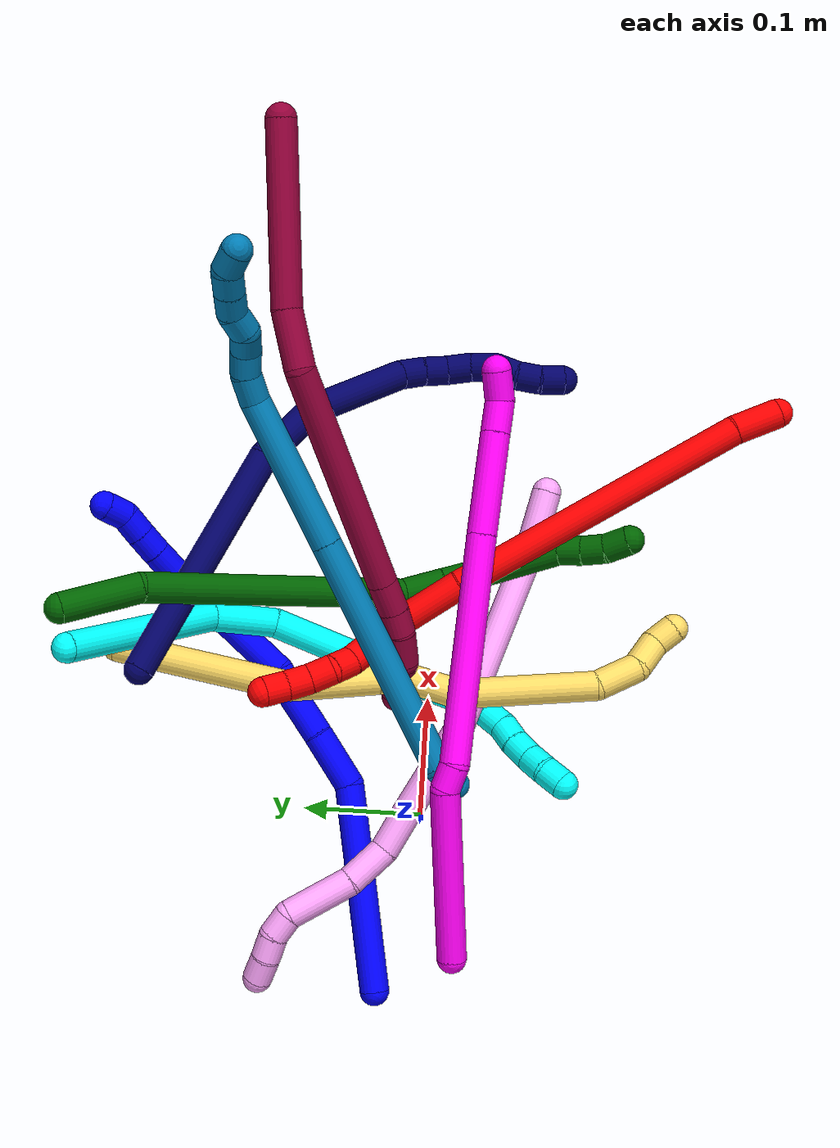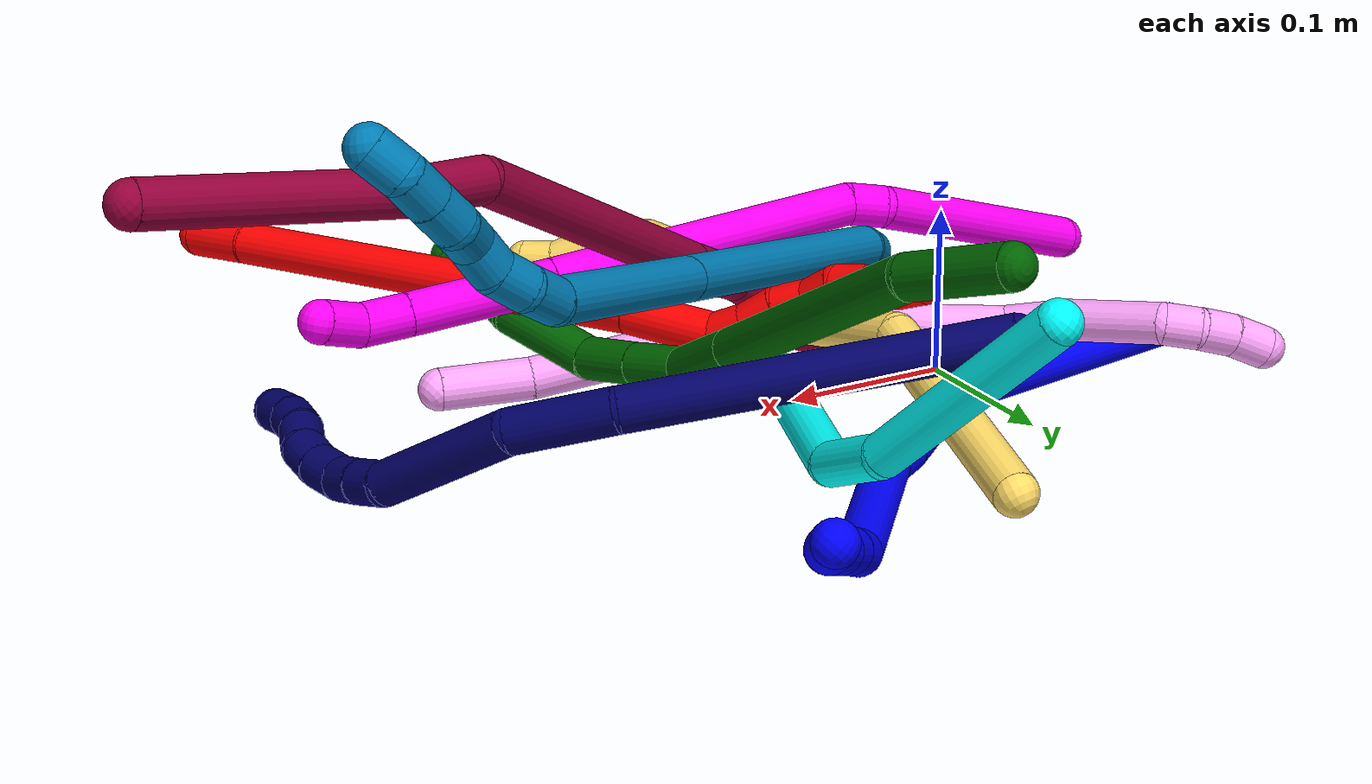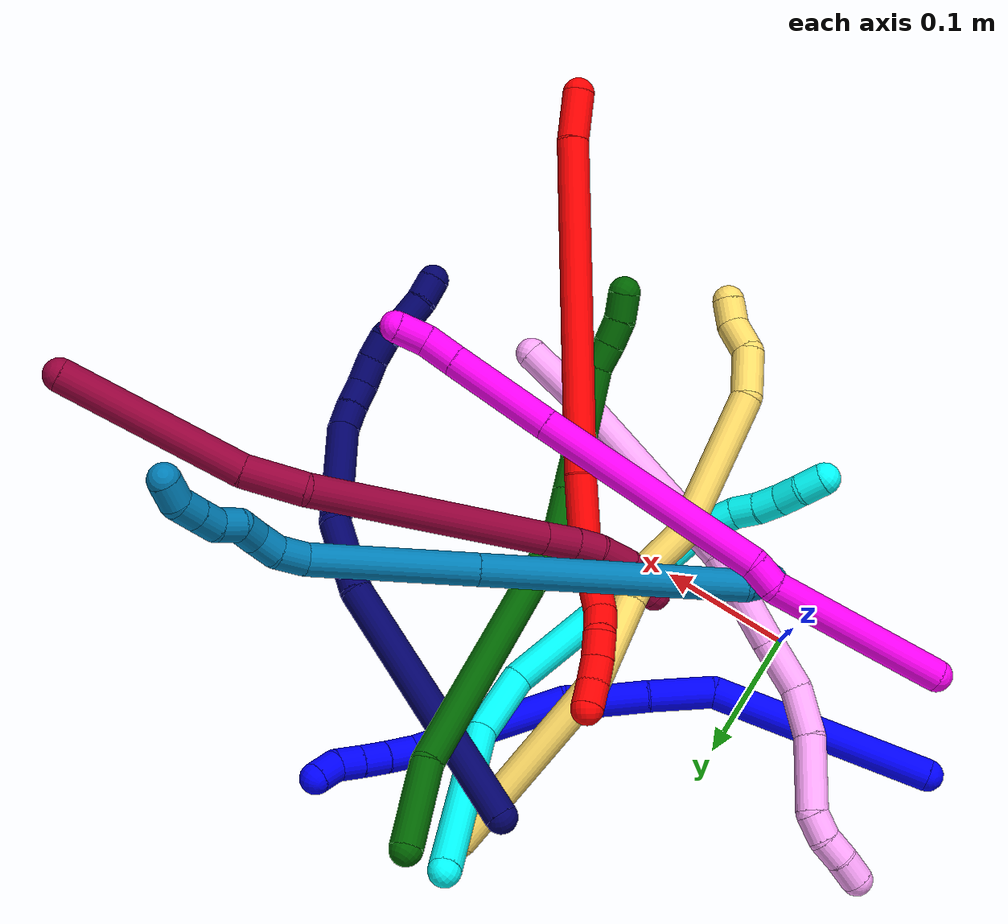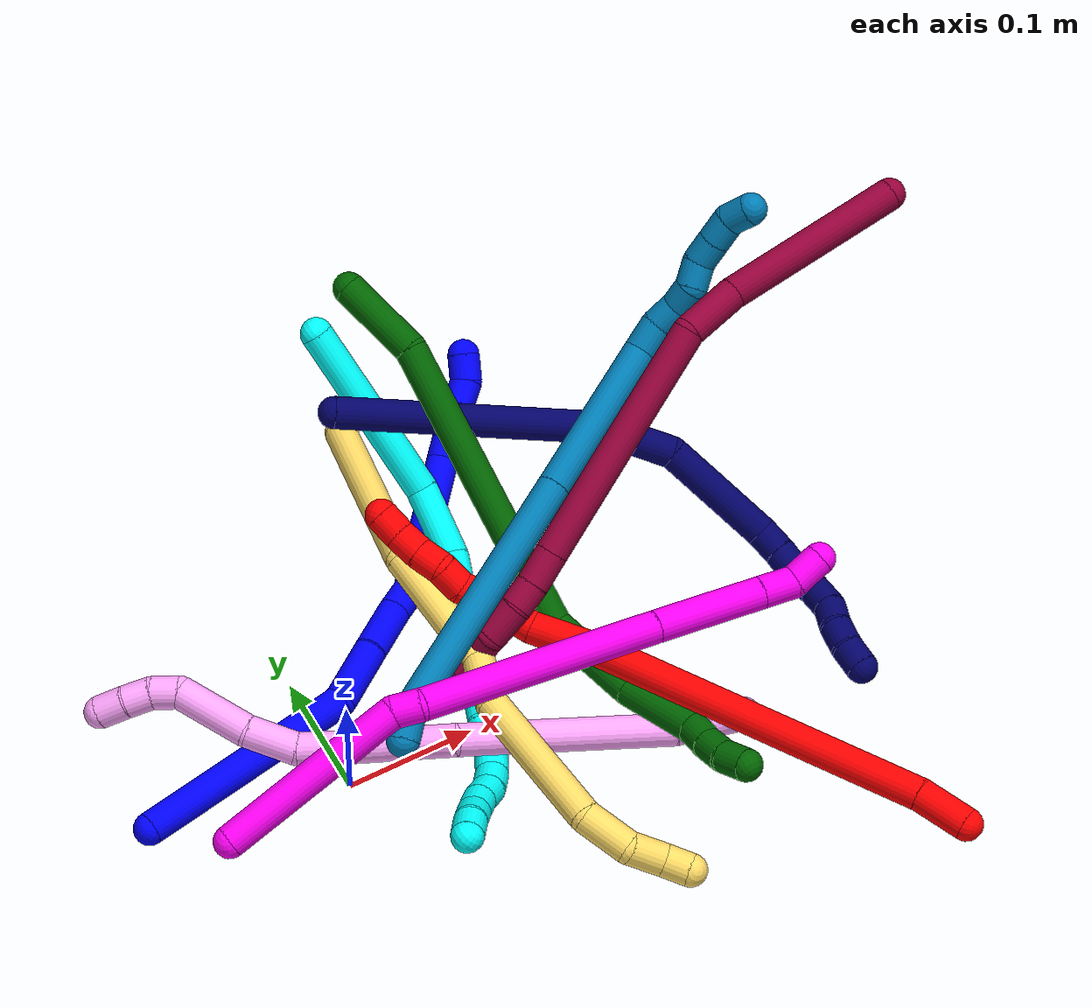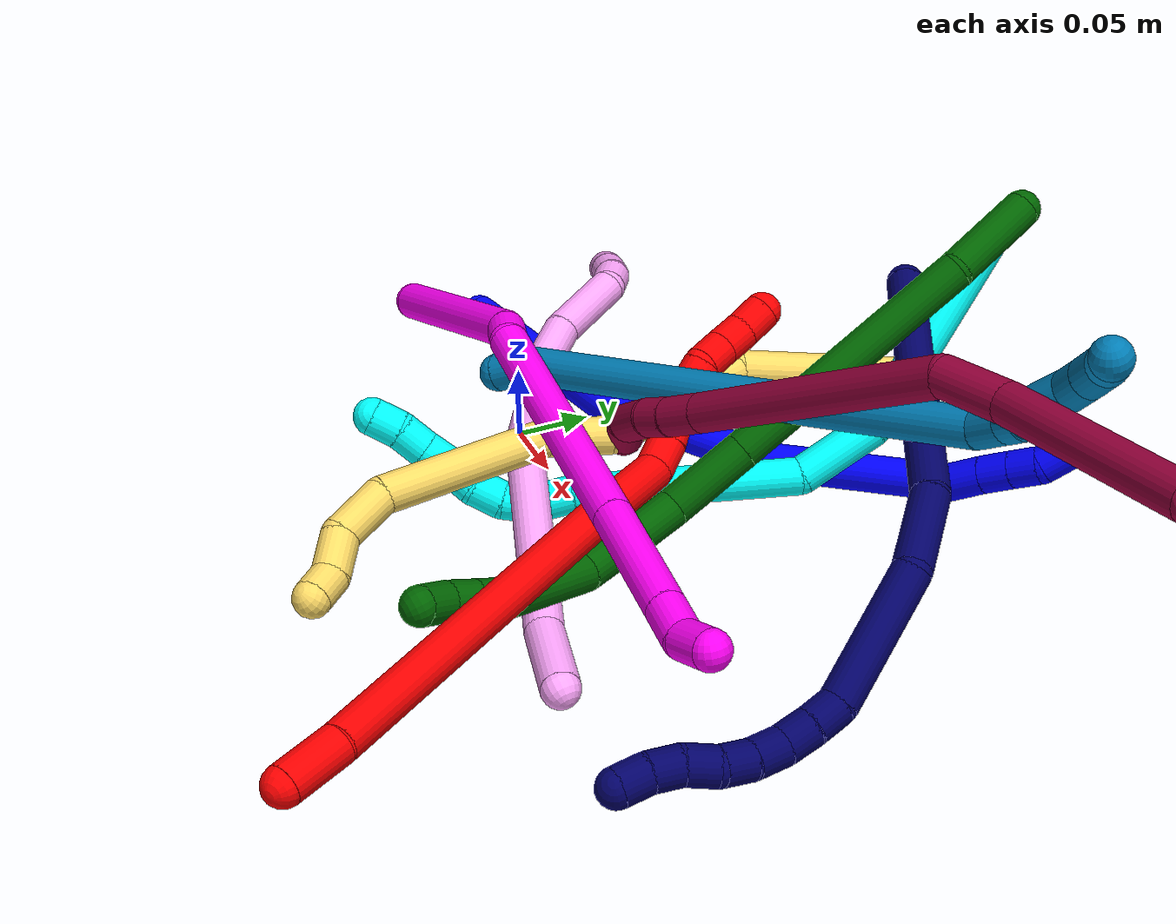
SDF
<sdf version="1.7">
 <world name="default">
  <plugin name="TubeGeneratorPlugin" filename="libtube_generator_plugin.so"/>
  <model name="photoneo_s_sensor">
   <static>1</static>
   <pose>0 0 2 1.57079 1.57079 3.14159</pose>
   <link name="link">
    <inertial><mass>0.1</mass></inertial>
    <sensor name="sensor" type="depth">
     <update_rate>30</update_rate>
     <camera>
      <horizontal_fov>1.22</horizontal_fov>
      <image><width>1920</width><height>1200</height><format>B8G8R8</format></image>
      <clip><near>0.1</near><far>2</far></clip>
      <depth_camera><output>points</output></depth_camera>
     </camera>
     <plugin name="camera_plugin" filename="libgazebo_ros_depth_camera.so">
      <baseline>0.2</baseline>
      <alwaysOn>1</alwaysOn>
      <updateRate>0.0</updateRate>
      <cameraName>camera_ir</cameraName>
      <imageTopicName>/camera/color/image_raw</imageTopicName>
      <cameraInfoTopicName>/camera/color/camera_info</cameraInfoTopicName>
      <depthImageTopicName>/camera/depth/image_raw</depthImageTopicName>
      <depthImageCameraInfoTopicName>/camera/depth/camera_info</depthImageCameraInfoTopicName>
      <pointCloudTopicName>/camera/depth/points</pointCloudTopicName>
      <frameName>fr_optical</frameName>
      <pointCloudCutoff>0.1</pointCloudCutoff>
      <pointCloudCutoffMax>2.0</pointCloudCutoffMax>
      <distortionK1>0</distortionK1>
      <distortionK2>0</distortionK2>
      <distortionK3>0</distortionK3>
      <distortionT1>0</distortionT1>
      <distortionT2>0</distortionT2>
      <CxPrime>0</CxPrime>
      <Cx>0</Cx>
      <Cy>0</Cy>
      <focalLength>0</focalLength>
      <hackBaseline>0</hackBaseline>
     </plugin>
    </sensor>
   </link>
  </model>
  <gravity>0 0 -9.8</gravity>
  <magnetic_field>6e-06 2.3e-05 -4.2e-05</magnetic_field>
  <atmosphere type="adiabatic"/>
  <physics name="default_physics" default="0" type="ode">
   <max_step_size>0.003</max_step_size>
   <real_time_factor>1</real_time_factor>
   <real_time_update_rate>1000</real_time_update_rate>
   <max_contacts>10000</max_contacts>
   <ode>
    <solver>
     <type>quick</type>
     <iters>100</iters>
     <sor>1.3</sor>
     <use_dynamic_moi_rescaling>0</use_dynamic_moi_rescaling>
    </solver>
    <constraints>
     <contact_max_correcting_vel>0</contact_max_correcting_vel>
     <contact_surface_layer>0.001</contact_surface_layer>
     <cfm>0</cfm>
     <erp>0.2</erp>
    </constraints>
   </ode>
  </physics>
  <scene><ambient>0.4 0.4 0.4 1</ambient><background>0.7 0.7 0.7 1</background><shadows>0</shadows></scene>
  <audio><device>default</device></audio>
  <spherical_coordinates>
   <surface_model>EARTH_WGS84</surface_model>
   <latitude_deg>0</latitude_deg>
   <longitude_deg>0</longitude_deg>
   <elevation>0</elevation>
   <heading_deg>0</heading_deg>
  </spherical_coordinates>
  <model name="bin">
   <static>1</static>
   <link name="bottom">
    <collision name="collision-bottom">
     <pose>0 0 -0.01 0 -0 0</pose>
     <geometry><box><size>0.8 0.6 0.02</size></box></geometry>
     <surface>
      <friction><ode><mu>100</mu><mu2>100</mu2></ode></friction>
      <contact><collide_bitmask>65535</collide_bitmask></contact>
     </surface>
    </collision>
   </link>
   <link name="west_wall">
    <collision name="collision-west_wall">
     <pose>-0.41 0 0.1 0 -0 0</pose>
     <geometry><box><size>0.02 0.6 0.2</size></box></geometry>
     <surface>
      <friction><ode><mu>100</mu><mu2>100</mu2></ode></friction>
      <contact><collide_bitmask>65535</collide_bitmask></contact>
     </surface>
    </collision>
   </link>
   <link name="east_wall">
    <collision name="collision-east_wall">
     <pose>0.41 0 0.1 0 -0 0</pose>
     <geometry><box><size>0.02 0.6 0.2</size></box></geometry>
     <surface>
      <friction><ode><mu>100</mu><mu2>100</mu2></ode></friction>
      <contact><collide_bitmask>65535</collide_bitmask></contact>
     </surface>
    </collision>
   </link>
   <link name="south_wall">
    <collision name="collision-south_wall">
     <pose>0 -0.31 0.1 0 -0 0</pose>
     <geometry><box><size>0.8 0.02 0.2</size></box></geometry>
     <surface>
      <friction><ode><mu>100</mu><mu2>100</mu2></ode></friction>
      <contact><collide_bitmask>65535</collide_bitmask></contact>
     </surface>
    </collision>
   </link>
   <link name="north_wall">
    <collision name="collision-north_wall">
     <pose>0 0.31 0.1 0 -0 0</pose>
     <geometry><box><size>0.8 0.02 0.2</size></box></geometry>
     <surface>
      <friction><ode><mu>100</mu><mu2>100</mu2></ode></friction>
      <contact><collide_bitmask>65535</collide_bitmask></contact>
     </surface>
    </collision>
   </link>
  </model>
  <model name="1">
   <static>0</static>
   <link name="1">
    <collision name="collision-cylinder-e_1_1_4">
     <pose>0.042503 0.049941 0.058399 -0.707487 0.505242 -0.190072</pose>
     <geometry><cylinder><radius>0.0125</radius><length>0.175625</length></cylinder></geometry>
     <surface>
      <friction><ode><mu>1.16</mu><mu2>1.16</mu2><slip1>0</slip1><slip2>0</slip2></ode></friction>
      <contact><ode><kp>1e+06</kp><kd>1</kd><max_vel>0</max_vel><min_depth>0.001</min_depth></ode></contact>
     </surface>
    </collision>
    <visual name="visual-cylinder-e_1_1_4">
     <pose>0.042503 0.049941 0.058399 -0.707487 0.505242 -0.190072</pose>
     <geometry><cylinder><radius>0.0125</radius><length>0.175625</length></cylinder></geometry>
     <material><ambient>0 0 1 1</ambient></material>
    </visual>
    <collision name="collision-cylinder-e_2_4_5">
     <pose>0.105161 0.108243 0.129117 -0.596309 0.934554 -0.307659</pose>
     <geometry><cylinder><radius>0.0125</radius><length>0.050116</length></cylinder></geometry>
     <surface>
      <friction><ode><mu>1.16</mu><mu2>1.16</mu2><slip1>0</slip1><slip2>0</slip2></ode></friction>
      <contact><ode><kp>1e+06</kp><kd>1</kd><max_vel>0</max_vel><min_depth>0.001</min_depth></ode></contact>
     </surface>
    </collision>
    <visual name="visual-cylinder-e_2_4_5">
     <pose>0.105161 0.108243 0.129117 -0.596309 0.934554 -0.307659</pose>
     <geometry><cylinder><radius>0.0125</radius><length>0.050116</length></cylinder></geometry>
     <material><ambient>0 0 1 1</ambient></material>
    </visual>
    <collision name="collision-cylinder-e_3_5_6">
     <pose>0.142167 0.121653 0.153163 -0.406555 0.922423 -0.204158</pose>
     <geometry><cylinder><radius>0.0125</radius><length>0.042284</length></cylinder></geometry>
     <surface>
      <friction><ode><mu>1.16</mu><mu2>1.16</mu2><slip1>0</slip1><slip2>0</slip2></ode></friction>
      <contact><ode><kp>1e+06</kp><kd>1</kd><max_vel>0</max_vel><min_depth>0.001</min_depth></ode></contact>
     </surface>
    </collision>
    <visual name="visual-cylinder-e_3_5_6">
     <pose>0.142167 0.121653 0.153163 -0.406555 0.922423 -0.204158</pose>
     <geometry><cylinder><radius>0.0125</radius><length>0.042284</length></cylinder></geometry>
     <material><ambient>0 0 1 1</ambient></material>
    </visual>
    <collision name="collision-cylinder-e_4_6_7">
     <pose>0.167612 0.130767 0.171015 -0.585884 0.86318 -0.276053</pose>
     <geometry><cylinder><radius>0.0125</radius><length>0.022617</length></cylinder></geometry>
     <surface>
      <friction><ode><mu>1.16</mu><mu2>1.16</mu2><slip1>0</slip1><slip2>0</slip2></ode></friction>
      <contact><ode><kp>1e+06</kp><kd>1</kd><max_vel>0</max_vel><min_depth>0.001</min_depth></ode></contact>
     </surface>
    </collision>
    <visual name="visual-cylinder-e_4_6_7">
     <pose>0.167612 0.130767 0.171015 -0.585884 0.86318 -0.276053</pose>
     <geometry><cylinder><radius>0.0125</radius><length>0.022617</length></cylinder></geometry>
     <material><ambient>0 0 1 1</ambient></material>
    </visual>
    <collision name="collision-cylinder-e_5_7_8">
     <pose>0.232506 0.144296 0.198725 -0.41324 1.17433 -0.277187</pose>
     <geometry><cylinder><radius>0.0125</radius><length>0.12207</length></cylinder></geometry>
     <surface>
      <friction><ode><mu>1.16</mu><mu2>1.16</mu2><slip1>0</slip1><slip2>0</slip2></ode></friction>
      <contact><ode><kp>1e+06</kp><kd>1</kd><max_vel>0</max_vel><min_depth>0.001</min_depth></ode></contact>
     </surface>
    </collision>
    <visual name="visual-cylinder-e_5_7_8">
     <pose>0.232506 0.144296 0.198725 -0.41324 1.17433 -0.277187</pose>
     <geometry><cylinder><radius>0.0125</radius><length>0.12207</length></cylinder></geometry>
     <material><ambient>0 0 1 1</ambient></material>
    </visual>
    <collision name="collision-cylinder-e_6_8_9">
     <pose>0.299891 0.159806 0.221074 -1.44499 1.0682 -0.961157</pose>
     <geometry><cylinder><radius>0.0125</radius><length>0.025297</length></cylinder></geometry>
     <surface>
      <friction><ode><mu>1.16</mu><mu2>1.16</mu2><slip1>0</slip1><slip2>0</slip2></ode></friction>
      <contact><ode><kp>1e+06</kp><kd>1</kd><max_vel>0</max_vel><min_depth>0.001</min_depth></ode></contact>
     </surface>
    </collision>
    <visual name="visual-cylinder-e_6_8_9">
     <pose>0.299891 0.159806 0.221074 -1.44499 1.0682 -0.961157</pose>
     <geometry><cylinder><radius>0.0125</radius><length>0.025297</length></cylinder></geometry>
     <material><ambient>0 0 1 1</ambient></material>
    </visual>
    <collision name="collision-cylinder-e_7_9_10">
     <pose>0.320028 0.170877 0.223045 -1.33529 1.05195 -0.858476</pose>
     <geometry><cylinder><radius>0.0125</radius><length>0.020848</length></cylinder></geometry>
     <surface>
      <friction><ode><mu>1.16</mu><mu2>1.16</mu2><slip1>0</slip1><slip2>0</slip2></ode></friction>
      <contact><ode><kp>1e+06</kp><kd>1</kd><max_vel>0</max_vel><min_depth>0.001</min_depth></ode></contact>
     </surface>
    </collision>
    <visual name="visual-cylinder-e_7_9_10">
     <pose>0.320028 0.170877 0.223045 -1.33529 1.05195 -0.858476</pose>
     <geometry><cylinder><radius>0.0125</radius><length>0.020848</length></cylinder></geometry>
     <material><ambient>0 0 1 1</ambient></material>
    </visual>
    <collision name="collision-cylinder-e_8_10_11">
     <pose>0.337693 0.180948 0.225523 -1.32376 1.02748 -0.828411</pose>
     <geometry><cylinder><radius>0.0125</radius><length>0.020125</length></cylinder></geometry>
     <surface>
      <friction><ode><mu>1.16</mu><mu2>1.16</mu2><slip1>0</slip1><slip2>0</slip2></ode></friction>
      <contact><ode><kp>1e+06</kp><kd>1</kd><max_vel>0</max_vel><min_depth>0.001</min_depth></ode></contact>
     </surface>
    </collision>
    <visual name="visual-cylinder-e_8_10_11">
     <pose>0.337693 0.180948 0.225523 -1.32376 1.02748 -0.828411</pose>
     <geometry><cylinder><radius>0.0125</radius><length>0.020125</length></cylinder></geometry>
     <material><ambient>0 0 1 1</ambient></material>
    </visual>
    <collision name="collision-cylinder-e_9_11_2">
     <pose>0.355999 0.189137 0.224225 -2.25608 1.17394 -1.90303</pose>
     <geometry><cylinder><radius>0.0125</radius><length>0.021019</length></cylinder></geometry>
     <surface>
      <friction><ode><mu>1.16</mu><mu2>1.16</mu2><slip1>0</slip1><slip2>0</slip2></ode></friction>
      <contact><ode><kp>1e+06</kp><kd>1</kd><max_vel>0</max_vel><min_depth>0.001</min_depth></ode></contact>
     </surface>
    </collision>
    <visual name="visual-cylinder-e_9_11_2">
     <pose>0.355999 0.189137 0.224225 -2.25608 1.17394 -1.90303</pose>
     <geometry><cylinder><radius>0.0125</radius><length>0.021019</length></cylinder></geometry>
     <material><ambient>0 0 1 1</ambient></material>
    </visual>
    <collision name="collision-sphere-2">
     <pose>0.365692 0.192282 0.221654 0 -0 0</pose>
     <geometry><sphere><radius>0.0125</radius></sphere></geometry>
     <surface>
      <friction><ode><mu>1.16</mu><mu2>1.16</mu2><slip1>0</slip1><slip2>0</slip2></ode></friction>
      <contact><ode><kp>1e+06</kp><kd>1</kd><max_vel>0</max_vel><min_depth>0.001</min_depth></ode></contact>
     </surface>
    </collision>
    <visual name="visual-sphere-2">
     <pose>0.365692 0.192282 0.221654 0 -0 0</pose>
     <geometry><sphere><radius>0.0125</radius></sphere></geometry>
     <material><ambient>0 0 1 1</ambient></material>
    </visual>
    <collision name="collision-sphere-11">
     <pose>0.346306 0.185992 0.226795 0 -0 0</pose>
     <geometry><sphere><radius>0.0125</radius></sphere></geometry>
     <surface>
      <friction><ode><mu>1.16</mu><mu2>1.16</mu2><slip1>0</slip1><slip2>0</slip2></ode></friction>
      <contact><ode><kp>1e+06</kp><kd>1</kd><max_vel>0</max_vel><min_depth>0.001</min_depth></ode></contact>
     </surface>
    </collision>
    <visual name="visual-sphere-11">
     <pose>0.346306 0.185992 0.226795 0 -0 0</pose>
     <geometry><sphere><radius>0.0125</radius></sphere></geometry>
     <material><ambient>0 0 1 1</ambient></material>
    </visual>
    <collision name="collision-sphere-10">
     <pose>0.32908 0.175904 0.224251 0 -0 0</pose>
     <geometry><sphere><radius>0.0125</radius></sphere></geometry>
     <surface>
      <friction><ode><mu>1.16</mu><mu2>1.16</mu2><slip1>0</slip1><slip2>0</slip2></ode></friction>
      <contact><ode><kp>1e+06</kp><kd>1</kd><max_vel>0</max_vel><min_depth>0.001</min_depth></ode></contact>
     </surface>
    </collision>
    <visual name="visual-sphere-10">
     <pose>0.32908 0.175904 0.224251 0 -0 0</pose>
     <geometry><sphere><radius>0.0125</radius></sphere></geometry>
     <material><ambient>0 0 1 1</ambient></material>
    </visual>
    <collision name="collision-sphere-9">
     <pose>0.310975 0.165851 0.221839 0 -0 0</pose>
     <geometry><sphere><radius>0.0125</radius></sphere></geometry>
     <surface>
      <friction><ode><mu>1.16</mu><mu2>1.16</mu2><slip1>0</slip1><slip2>0</slip2></ode></friction>
      <contact><ode><kp>1e+06</kp><kd>1</kd><max_vel>0</max_vel><min_depth>0.001</min_depth></ode></contact>
     </surface>
    </collision>
    <visual name="visual-sphere-9">
     <pose>0.310975 0.165851 0.221839 0 -0 0</pose>
     <geometry><sphere><radius>0.0125</radius></sphere></geometry>
     <material><ambient>0 0 1 1</ambient></material>
    </visual>
    <collision name="collision-sphere-4">
     <pose>0.085006 0.099882 0.116798 0 -0 0</pose>
     <geometry><sphere><radius>0.0125</radius></sphere></geometry>
     <surface>
      <friction><ode><mu>1.16</mu><mu2>1.16</mu2><slip1>0</slip1><slip2>0</slip2></ode></friction>
      <contact><ode><kp>1e+06</kp><kd>1</kd><max_vel>0</max_vel><min_depth>0.001</min_depth></ode></contact>
     </surface>
    </collision>
    <visual name="visual-sphere-4">
     <pose>0.085006 0.099882 0.116798 0 -0 0</pose>
     <geometry><sphere><radius>0.0125</radius></sphere></geometry>
     <material><ambient>0 0 1 1</ambient></material>
    </visual>
    <collision name="collision-sphere-1">
     <geometry><sphere><radius>0.0125</radius></sphere></geometry>
     <surface>
      <friction><ode><mu>1.16</mu><mu2>1.16</mu2><slip1>0</slip1><slip2>0</slip2></ode></friction>
      <contact><ode><kp>1e+06</kp><kd>1</kd><max_vel>0</max_vel><min_depth>0.001</min_depth></ode></contact>
     </surface>
    </collision>
    <visual name="visual-sphere-1">
     <geometry><sphere><radius>0.0125</radius></sphere></geometry>
     <material><ambient>0 0 1 1</ambient></material>
    </visual>
    <collision name="collision-sphere-8">
     <pose>0.288806 0.153761 0.22031 0 -0 0</pose>
     <geometry><sphere><radius>0.0125</radius></sphere></geometry>
     <surface>
      <friction><ode><mu>1.16</mu><mu2>1.16</mu2><slip1>0</slip1><slip2>0</slip2></ode></friction>
      <contact><ode><kp>1e+06</kp><kd>1</kd><max_vel>0</max_vel><min_depth>0.001</min_depth></ode></contact>
     </surface>
    </collision>
    <visual name="visual-sphere-8">
     <pose>0.288806 0.153761 0.22031 0 -0 0</pose>
     <geometry><sphere><radius>0.0125</radius></sphere></geometry>
     <material><ambient>0 0 1 1</ambient></material>
    </visual>
    <collision name="collision-sphere-5">
     <pose>0.125315 0.116605 0.141436 0 -0 0</pose>
     <geometry><sphere><radius>0.0125</radius></sphere></geometry>
     <surface>
      <friction><ode><mu>1.16</mu><mu2>1.16</mu2><slip1>0</slip1><slip2>0</slip2></ode></friction>
      <contact><ode><kp>1e+06</kp><kd>1</kd><max_vel>0</max_vel><min_depth>0.001</min_depth></ode></contact>
     </surface>
    </collision>
    <visual name="visual-sphere-5">
     <pose>0.125315 0.116605 0.141436 0 -0 0</pose>
     <geometry><sphere><radius>0.0125</radius></sphere></geometry>
     <material><ambient>0 0 1 1</ambient></material>
    </visual>
    <collision name="collision-sphere-6">
     <pose>0.159018 0.126702 0.16489 0 -0 0</pose>
     <geometry><sphere><radius>0.0125</radius></sphere></geometry>
     <surface>
      <friction><ode><mu>1.16</mu><mu2>1.16</mu2><slip1>0</slip1><slip2>0</slip2></ode></friction>
      <contact><ode><kp>1e+06</kp><kd>1</kd><max_vel>0</max_vel><min_depth>0.001</min_depth></ode></contact>
     </surface>
    </collision>
    <visual name="visual-sphere-6">
     <pose>0.159018 0.126702 0.16489 0 -0 0</pose>
     <geometry><sphere><radius>0.0125</radius></sphere></geometry>
     <material><ambient>0 0 1 1</ambient></material>
    </visual>
    <collision name="collision-sphere-7">
     <pose>0.176206 0.134831 0.177139 0 -0 0</pose>
     <geometry><sphere><radius>0.0125</radius></sphere></geometry>
     <surface>
      <friction><ode><mu>1.16</mu><mu2>1.16</mu2><slip1>0</slip1><slip2>0</slip2></ode></friction>
      <contact><ode><kp>1e+06</kp><kd>1</kd><max_vel>0</max_vel><min_depth>0.001</min_depth></ode></contact>
     </surface>
    </collision>
    <visual name="visual-sphere-7">
     <pose>0.176206 0.134831 0.177139 0 -0 0</pose>
     <geometry><sphere><radius>0.0125</radius></sphere></geometry>
     <material><ambient>0 0 1 1</ambient></material>
    </visual>
    <inertial>
     <pose>0.158912 0.110267 0.141647 0 -0 0</pose>
     <mass>0.5</mass>
     <inertia>
      <ixx>0.000396</ixx>
      <ixy>0</ixy>
      <ixz>0</ixz>
      <iyy>0.000466</iyy>
      <iyz>0</iyz>
      <izz>-0.000667</izz>
     </inertia>
    </inertial>
   </link>
   <pose>-0.149363 0.029509 0.011775 2.37547 -0.190619 1.24458</pose>
  </model>
  <model name="2">
   <static>0</static>
   <link name="2">
    <collision name="collision-cylinder-e_1_1_4">
     <pose>0.000374 0.00381 -0.019449 -2.94814 0.018851 -0.193676</pose>
     <geometry><cylinder><radius>0.0125</radius><length>0.039644</length></cylinder></geometry>
     <surface>
      <friction><ode><mu>1.16</mu><mu2>1.16</mu2><slip1>0</slip1><slip2>0</slip2></ode></friction>
      <contact><ode><kp>1e+06</kp><kd>1</kd><max_vel>0</max_vel><min_depth>0.001</min_depth></ode></contact>
     </surface>
    </collision>
    <visual name="visual-cylinder-e_1_1_4">
     <pose>0.000374 0.00381 -0.019449 -2.94814 0.018851 -0.193676</pose>
     <geometry><cylinder><radius>0.0125</radius><length>0.039644</length></cylinder></geometry>
     <material><ambient>1 0 0 1</ambient></material>
    </visual>
    <collision name="collision-cylinder-e_2_4_5">
     <pose>-0.003944 0.014572 -0.170513 -3.08882 -0.035578 1.18635</pose>
     <geometry><cylinder><radius>0.0125</radius><length>0.263764</length></cylinder></geometry>
     <surface>
      <friction><ode><mu>1.16</mu><mu2>1.16</mu2><slip1>0</slip1><slip2>0</slip2></ode></friction>
      <contact><ode><kp>1e+06</kp><kd>1</kd><max_vel>0</max_vel><min_depth>0.001</min_depth></ode></contact>
     </surface>
    </collision>
    <visual name="visual-cylinder-e_2_4_5">
     <pose>-0.003944 0.014572 -0.170513 -3.08882 -0.035578 1.18635</pose>
     <geometry><cylinder><radius>0.0125</radius><length>0.263764</length></cylinder></geometry>
     <material><ambient>1 0 0 1</ambient></material>
    </visual>
    <collision name="collision-cylinder-e_3_5_6">
     <pose>-0.008804 0.020269 -0.329121 3.09517 -0.006268 -0.268342</pose>
     <geometry><cylinder><radius>0.0125</radius><length>0.054046</length></cylinder></geometry>
     <surface>
      <friction><ode><mu>1.16</mu><mu2>1.16</mu2><slip1>0</slip1><slip2>0</slip2></ode></friction>
      <contact><ode><kp>1e+06</kp><kd>1</kd><max_vel>0</max_vel><min_depth>0.001</min_depth></ode></contact>
     </surface>
    </collision>
    <visual name="visual-cylinder-e_3_5_6">
     <pose>-0.008804 0.020269 -0.329121 3.09517 -0.006268 -0.268342</pose>
     <geometry><cylinder><radius>0.0125</radius><length>0.054046</length></cylinder></geometry>
     <material><ambient>1 0 0 1</ambient></material>
    </visual>
    <collision name="collision-cylinder-e_4_6_7">
     <pose>-0.013136 0.022044 -0.365566 -2.83149 -0.397108 1.82068</pose>
     <geometry><cylinder><radius>0.0125</radius><length>0.021526</length></cylinder></geometry>
     <surface>
      <friction><ode><mu>1.16</mu><mu2>1.16</mu2><slip1>0</slip1><slip2>0</slip2></ode></friction>
      <contact><ode><kp>1e+06</kp><kd>1</kd><max_vel>0</max_vel><min_depth>0.001</min_depth></ode></contact>
     </surface>
    </collision>
    <visual name="visual-cylinder-e_4_6_7">
     <pose>-0.013136 0.022044 -0.365566 -2.83149 -0.397108 1.82068</pose>
     <geometry><cylinder><radius>0.0125</radius><length>0.021526</length></cylinder></geometry>
     <material><ambient>1 0 0 1</ambient></material>
    </visual>
    <collision name="collision-cylinder-e_5_7_8">
     <pose>-0.022884 0.028282 -0.38281 -2.75081 -0.585287 1.97918</pose>
     <geometry><cylinder><radius>0.0125</radius><length>0.020219</length></cylinder></geometry>
     <surface>
      <friction><ode><mu>1.16</mu><mu2>1.16</mu2><slip1>0</slip1><slip2>0</slip2></ode></friction>
      <contact><ode><kp>1e+06</kp><kd>1</kd><max_vel>0</max_vel><min_depth>0.001</min_depth></ode></contact>
     </surface>
    </collision>
    <visual name="visual-cylinder-e_5_7_8">
     <pose>-0.022884 0.028282 -0.38281 -2.75081 -0.585287 1.97918</pose>
     <geometry><cylinder><radius>0.0125</radius><length>0.020219</length></cylinder></geometry>
     <material><ambient>1 0 0 1</ambient></material>
    </visual>
    <collision name="collision-cylinder-e_6_8_9">
     <pose>-0.032126 0.033305 -0.399921 -2.94943 -0.367724 2.18529</pose>
     <geometry><cylinder><radius>0.0125</radius><length>0.02035</length></cylinder></geometry>
     <surface>
      <friction><ode><mu>1.16</mu><mu2>1.16</mu2><slip1>0</slip1><slip2>0</slip2></ode></friction>
      <contact><ode><kp>1e+06</kp><kd>1</kd><max_vel>0</max_vel><min_depth>0.001</min_depth></ode></contact>
     </surface>
    </collision>
    <visual name="visual-cylinder-e_6_8_9">
     <pose>-0.032126 0.033305 -0.399921 -2.94943 -0.367724 2.18529</pose>
     <geometry><cylinder><radius>0.0125</radius><length>0.02035</length></cylinder></geometry>
     <material><ambient>1 0 0 1</ambient></material>
    </visual>
    <collision name="collision-cylinder-e_7_9_10">
     <pose>-0.039379 0.040178 -0.417232 -2.57715 -0.363283 1.12926</pose>
     <geometry><cylinder><radius>0.0125</radius><length>0.020236</length></cylinder></geometry>
     <surface>
      <friction><ode><mu>1.16</mu><mu2>1.16</mu2><slip1>0</slip1><slip2>0</slip2></ode></friction>
      <contact><ode><kp>1e+06</kp><kd>1</kd><max_vel>0</max_vel><min_depth>0.001</min_depth></ode></contact>
     </surface>
    </collision>
    <visual name="visual-cylinder-e_7_9_10">
     <pose>-0.039379 0.040178 -0.417232 -2.57715 -0.363283 1.12926</pose>
     <geometry><cylinder><radius>0.0125</radius><length>0.020236</length></cylinder></geometry>
     <material><ambient>1 0 0 1</ambient></material>
    </visual>
    <collision name="collision-cylinder-e_8_10_11">
     <pose>-0.043613 0.047729 -0.434968 -2.89125 -0.063378 0.493579</pose>
     <geometry><cylinder><radius>0.0125</radius><length>0.020158</length></cylinder></geometry>
     <surface>
      <friction><ode><mu>1.16</mu><mu2>1.16</mu2><slip1>0</slip1><slip2>0</slip2></ode></friction>
      <contact><ode><kp>1e+06</kp><kd>1</kd><max_vel>0</max_vel><min_depth>0.001</min_depth></ode></contact>
     </surface>
    </collision>
    <visual name="visual-cylinder-e_8_10_11">
     <pose>-0.043613 0.047729 -0.434968 -2.89125 -0.063378 0.493579</pose>
     <geometry><cylinder><radius>0.0125</radius><length>0.020158</length></cylinder></geometry>
     <material><ambient>1 0 0 1</ambient></material>
    </visual>
    <collision name="collision-cylinder-e_9_11_12">
     <pose>-0.044707 0.053989 -0.453978 -2.7554 -0.045497 0.231679</pose>
     <geometry><cylinder><radius>0.0125</radius><length>0.020025</length></cylinder></geometry>
     <surface>
      <friction><ode><mu>1.16</mu><mu2>1.16</mu2><slip1>0</slip1><slip2>0</slip2></ode></friction>
      <contact><ode><kp>1e+06</kp><kd>1</kd><max_vel>0</max_vel><min_depth>0.001</min_depth></ode></contact>
     </surface>
    </collision>
    <visual name="visual-cylinder-e_9_11_12">
     <pose>-0.044707 0.053989 -0.453978 -2.7554 -0.045497 0.231679</pose>
     <geometry><cylinder><radius>0.0125</radius><length>0.020025</length></cylinder></geometry>
     <material><ambient>1 0 0 1</ambient></material>
    </visual>
    <collision name="collision-cylinder-e_10_12_2">
     <pose>-0.04621 0.062521 -0.471992 -2.64279 -0.104752 0.405974</pose>
     <geometry><cylinder><radius>0.0125</radius><length>0.020032</length></cylinder></geometry>
     <surface>
      <friction><ode><mu>1.16</mu><mu2>1.16</mu2><slip1>0</slip1><slip2>0</slip2></ode></friction>
      <contact><ode><kp>1e+06</kp><kd>1</kd><max_vel>0</max_vel><min_depth>0.001</min_depth></ode></contact>
     </surface>
    </collision>
    <visual name="visual-cylinder-e_10_12_2">
     <pose>-0.04621 0.062521 -0.471992 -2.64279 -0.104752 0.405974</pose>
     <geometry><cylinder><radius>0.0125</radius><length>0.020032</length></cylinder></geometry>
     <material><ambient>1 0 0 1</ambient></material>
    </visual>
    <collision name="collision-sphere-2">
     <pose>-0.047257 0.067287 -0.480739 0 -0 0</pose>
     <geometry><sphere><radius>0.0125</radius></sphere></geometry>
     <surface>
      <friction><ode><mu>1.16</mu><mu2>1.16</mu2><slip1>0</slip1><slip2>0</slip2></ode></friction>
      <contact><ode><kp>1e+06</kp><kd>1</kd><max_vel>0</max_vel><min_depth>0.001</min_depth></ode></contact>
     </surface>
    </collision>
    <visual name="visual-sphere-2">
     <pose>-0.047257 0.067287 -0.480739 0 -0 0</pose>
     <geometry><sphere><radius>0.0125</radius></sphere></geometry>
     <material><ambient>1 0 0 1</ambient></material>
    </visual>
    <collision name="collision-sphere-12">
     <pose>-0.045162 0.057756 -0.463244 0 -0 0</pose>
     <geometry><sphere><radius>0.0125</radius></sphere></geometry>
     <surface>
      <friction><ode><mu>1.16</mu><mu2>1.16</mu2><slip1>0</slip1><slip2>0</slip2></ode></friction>
      <contact><ode><kp>1e+06</kp><kd>1</kd><max_vel>0</max_vel><min_depth>0.001</min_depth></ode></contact>
     </surface>
    </collision>
    <visual name="visual-sphere-12">
     <pose>-0.045162 0.057756 -0.463244 0 -0 0</pose>
     <geometry><sphere><radius>0.0125</radius></sphere></geometry>
     <material><ambient>1 0 0 1</ambient></material>
    </visual>
    <collision name="collision-sphere-11">
     <pose>-0.044252 0.050221 -0.444713 0 -0 0</pose>
     <geometry><sphere><radius>0.0125</radius></sphere></geometry>
     <surface>
      <friction><ode><mu>1.16</mu><mu2>1.16</mu2><slip1>0</slip1><slip2>0</slip2></ode></friction>
      <contact><ode><kp>1e+06</kp><kd>1</kd><max_vel>0</max_vel><min_depth>0.001</min_depth></ode></contact>
     </surface>
    </collision>
    <visual name="visual-sphere-11">
     <pose>-0.044252 0.050221 -0.444713 0 -0 0</pose>
     <geometry><sphere><radius>0.0125</radius></sphere></geometry>
     <material><ambient>1 0 0 1</ambient></material>
    </visual>
    <collision name="collision-sphere-10">
     <pose>-0.042975 0.045237 -0.425223 0 -0 0</pose>
     <geometry><sphere><radius>0.0125</radius></sphere></geometry>
     <surface>
      <friction><ode><mu>1.16</mu><mu2>1.16</mu2><slip1>0</slip1><slip2>0</slip2></ode></friction>
      <contact><ode><kp>1e+06</kp><kd>1</kd><max_vel>0</max_vel><min_depth>0.001</min_depth></ode></contact>
     </surface>
    </collision>
    <visual name="visual-sphere-10">
     <pose>-0.042975 0.045237 -0.425223 0 -0 0</pose>
     <geometry><sphere><radius>0.0125</radius></sphere></geometry>
     <material><ambient>1 0 0 1</ambient></material>
    </visual>
    <collision name="collision-sphere-9">
     <pose>-0.035784 0.035119 -0.409241 0 -0 0</pose>
     <geometry><sphere><radius>0.0125</radius></sphere></geometry>
     <surface>
      <friction><ode><mu>1.16</mu><mu2>1.16</mu2><slip1>0</slip1><slip2>0</slip2></ode></friction>
      <contact><ode><kp>1e+06</kp><kd>1</kd><max_vel>0</max_vel><min_depth>0.001</min_depth></ode></contact>
     </surface>
    </collision>
    <visual name="visual-sphere-9">
     <pose>-0.035784 0.035119 -0.409241 0 -0 0</pose>
     <geometry><sphere><radius>0.0125</radius></sphere></geometry>
     <material><ambient>1 0 0 1</ambient></material>
    </visual>
    <collision name="collision-sphere-4">
     <pose>0.000747 0.00762 -0.038898 0 -0 0</pose>
     <geometry><sphere><radius>0.0125</radius></sphere></geometry>
     <surface>
      <friction><ode><mu>1.16</mu><mu2>1.16</mu2><slip1>0</slip1><slip2>0</slip2></ode></friction>
      <contact><ode><kp>1e+06</kp><kd>1</kd><max_vel>0</max_vel><min_depth>0.001</min_depth></ode></contact>
     </surface>
    </collision>
    <visual name="visual-sphere-4">
     <pose>0.000747 0.00762 -0.038898 0 -0 0</pose>
     <geometry><sphere><radius>0.0125</radius></sphere></geometry>
     <material><ambient>1 0 0 1</ambient></material>
    </visual>
    <collision name="collision-sphere-1">
     <geometry><sphere><radius>0.0125</radius></sphere></geometry>
     <surface>
      <friction><ode><mu>1.16</mu><mu2>1.16</mu2><slip1>0</slip1><slip2>0</slip2></ode></friction>
      <contact><ode><kp>1e+06</kp><kd>1</kd><max_vel>0</max_vel><min_depth>0.001</min_depth></ode></contact>
     </surface>
    </collision>
    <visual name="visual-sphere-1">
     <geometry><sphere><radius>0.0125</radius></sphere></geometry>
     <material><ambient>1 0 0 1</ambient></material>
    </visual>
    <collision name="collision-sphere-8">
     <pose>-0.028468 0.031492 -0.390601 0 -0 0</pose>
     <geometry><sphere><radius>0.0125</radius></sphere></geometry>
     <surface>
      <friction><ode><mu>1.16</mu><mu2>1.16</mu2><slip1>0</slip1><slip2>0</slip2></ode></friction>
      <contact><ode><kp>1e+06</kp><kd>1</kd><max_vel>0</max_vel><min_depth>0.001</min_depth></ode></contact>
     </surface>
    </collision>
    <visual name="visual-sphere-8">
     <pose>-0.028468 0.031492 -0.390601 0 -0 0</pose>
     <geometry><sphere><radius>0.0125</radius></sphere></geometry>
     <material><ambient>1 0 0 1</ambient></material>
    </visual>
    <collision name="collision-sphere-5">
     <pose>-0.008635 0.021523 -0.302128 0 -0 0</pose>
     <geometry><sphere><radius>0.0125</radius></sphere></geometry>
     <surface>
      <friction><ode><mu>1.16</mu><mu2>1.16</mu2><slip1>0</slip1><slip2>0</slip2></ode></friction>
      <contact><ode><kp>1e+06</kp><kd>1</kd><max_vel>0</max_vel><min_depth>0.001</min_depth></ode></contact>
     </surface>
    </collision>
    <visual name="visual-sphere-5">
     <pose>-0.008635 0.021523 -0.302128 0 -0 0</pose>
     <geometry><sphere><radius>0.0125</radius></sphere></geometry>
     <material><ambient>1 0 0 1</ambient></material>
    </visual>
    <collision name="collision-sphere-6">
     <pose>-0.008974 0.019015 -0.356114 0 -0 0</pose>
     <geometry><sphere><radius>0.0125</radius></sphere></geometry>
     <surface>
      <friction><ode><mu>1.16</mu><mu2>1.16</mu2><slip1>0</slip1><slip2>0</slip2></ode></friction>
      <contact><ode><kp>1e+06</kp><kd>1</kd><max_vel>0</max_vel><min_depth>0.001</min_depth></ode></contact>
     </surface>
    </collision>
    <visual name="visual-sphere-6">
     <pose>-0.008974 0.019015 -0.356114 0 -0 0</pose>
     <geometry><sphere><radius>0.0125</radius></sphere></geometry>
     <material><ambient>1 0 0 1</ambient></material>
    </visual>
    <collision name="collision-sphere-7">
     <pose>-0.017299 0.025072 -0.375018 0 -0 0</pose>
     <geometry><sphere><radius>0.0125</radius></sphere></geometry>
     <surface>
      <friction><ode><mu>1.16</mu><mu2>1.16</mu2><slip1>0</slip1><slip2>0</slip2></ode></friction>
      <contact><ode><kp>1e+06</kp><kd>1</kd><max_vel>0</max_vel><min_depth>0.001</min_depth></ode></contact>
     </surface>
    </collision>
    <visual name="visual-sphere-7">
     <pose>-0.017299 0.025072 -0.375018 0 -0 0</pose>
     <geometry><sphere><radius>0.0125</radius></sphere></geometry>
     <material><ambient>1 0 0 1</ambient></material>
    </visual>
    <inertial>
     <pose>-0.012795 0.021846 -0.246077 0 -0 0</pose>
     <mass>0.5</mass>
     <inertia>
      <ixx>0.002025</ixx>
      <ixy>0</ixy>
      <ixz>0</ixz>
      <iyy>0.000836</iyy>
      <iyz>0</iyz>
      <izz>-6.5e-05</izz>
     </inertia>
    </inertial>
   </link>
   <pose>0.357165 -0.276734 0.0622 1.49144 0.731303 0.532167</pose>
  </model>
  <model name="3">
   <static>0</static>
   <link name="3">
    <collision name="collision-cylinder-e_1_1_4">
     <pose>0.029283 -0.063951 -0.01992 1.87276 0.412139 0.553531</pose>
     <geometry><cylinder><radius>0.0125</radius><length>0.146206</length></cylinder></geometry>
     <surface>
      <friction><ode><mu>1.16</mu><mu2>1.16</mu2><slip1>0</slip1><slip2>0</slip2></ode></friction>
      <contact><ode><kp>1e+06</kp><kd>1</kd><max_vel>0</max_vel><min_depth>0.001</min_depth></ode></contact>
     </surface>
    </collision>
    <visual name="visual-cylinder-e_1_1_4">
     <pose>0.029283 -0.063951 -0.01992 1.87276 0.412139 0.553531</pose>
     <geometry><cylinder><radius>0.0125</radius><length>0.146206</length></cylinder></geometry>
     <material><ambient>0.003922 1 0.996078 1</ambient></material>
    </visual>
    <collision name="collision-cylinder-e_2_4_5">
     <pose>0.058099 -0.155632 -0.047689 1.84662 -0.016202 -0.021424</pose>
     <geometry><cylinder><radius>0.0125</radius><length>0.057645</length></cylinder></geometry>
     <surface>
      <friction><ode><mu>1.16</mu><mu2>1.16</mu2><slip1>0</slip1><slip2>0</slip2></ode></friction>
      <contact><ode><kp>1e+06</kp><kd>1</kd><max_vel>0</max_vel><min_depth>0.001</min_depth></ode></contact>
     </surface>
    </collision>
    <visual name="visual-cylinder-e_2_4_5">
     <pose>0.058099 -0.155632 -0.047689 1.84662 -0.016202 -0.021424</pose>
     <geometry><cylinder><radius>0.0125</radius><length>0.057645</length></cylinder></geometry>
     <material><ambient>0.003922 1 0.996078 1</ambient></material>
    </visual>
    <collision name="collision-cylinder-e_3_5_6">
     <pose>0.020545 -0.245709 -0.071788 1.82576 -0.522293 -0.665917</pose>
     <geometry><cylinder><radius>0.0125</radius><length>0.148685</length></cylinder></geometry>
     <surface>
      <friction><ode><mu>1.16</mu><mu2>1.16</mu2><slip1>0</slip1><slip2>0</slip2></ode></friction>
      <contact><ode><kp>1e+06</kp><kd>1</kd><max_vel>0</max_vel><min_depth>0.001</min_depth></ode></contact>
     </surface>
    </collision>
    <visual name="visual-cylinder-e_3_5_6">
     <pose>0.020545 -0.245709 -0.071788 1.82576 -0.522293 -0.665917</pose>
     <geometry><cylinder><radius>0.0125</radius><length>0.148685</length></cylinder></geometry>
     <material><ambient>0.003922 1 0.996078 1</ambient></material>
    </visual>
    <collision name="collision-cylinder-e_4_6_7">
     <pose>-0.021001 -0.319684 -0.092244 1.91791 -0.346106 -0.488308</pose>
     <geometry><cylinder><radius>0.0125</radius><length>0.026286</length></cylinder></geometry>
     <surface>
      <friction><ode><mu>1.16</mu><mu2>1.16</mu2><slip1>0</slip1><slip2>0</slip2></ode></friction>
      <contact><ode><kp>1e+06</kp><kd>1</kd><max_vel>0</max_vel><min_depth>0.001</min_depth></ode></contact>
     </surface>
    </collision>
    <visual name="visual-cylinder-e_4_6_7">
     <pose>-0.021001 -0.319684 -0.092244 1.91791 -0.346106 -0.488308</pose>
     <geometry><cylinder><radius>0.0125</radius><length>0.026286</length></cylinder></geometry>
     <material><ambient>0.003922 1 0.996078 1</ambient></material>
    </visual>
    <collision name="collision-cylinder-e_5_7_8">
     <pose>-0.032267 -0.338796 -0.098559 1.84543 -0.718988 -0.921446</pose>
     <geometry><cylinder><radius>0.0125</radius><length>0.020672</length></cylinder></geometry>
     <surface>
      <friction><ode><mu>1.16</mu><mu2>1.16</mu2><slip1>0</slip1><slip2>0</slip2></ode></friction>
      <contact><ode><kp>1e+06</kp><kd>1</kd><max_vel>0</max_vel><min_depth>0.001</min_depth></ode></contact>
     </surface>
    </collision>
    <visual name="visual-cylinder-e_5_7_8">
     <pose>-0.032267 -0.338796 -0.098559 1.84543 -0.718988 -0.921446</pose>
     <geometry><cylinder><radius>0.0125</radius><length>0.020672</length></cylinder></geometry>
     <material><ambient>0.003922 1 0.996078 1</ambient></material>
    </visual>
    <collision name="collision-cylinder-e_6_8_9">
     <pose>-0.047885 -0.351312 -0.101465 1.72792 -1.04666 -1.18833</pose>
     <geometry><cylinder><radius>0.0125</radius><length>0.020352</length></cylinder></geometry>
     <surface>
      <friction><ode><mu>1.16</mu><mu2>1.16</mu2><slip1>0</slip1><slip2>0</slip2></ode></friction>
      <contact><ode><kp>1e+06</kp><kd>1</kd><max_vel>0</max_vel><min_depth>0.001</min_depth></ode></contact>
     </surface>
    </collision>
    <visual name="visual-cylinder-e_6_8_9">
     <pose>-0.047885 -0.351312 -0.101465 1.72792 -1.04666 -1.18833</pose>
     <geometry><cylinder><radius>0.0125</radius><length>0.020352</length></cylinder></geometry>
     <material><ambient>0.003922 1 0.996078 1</ambient></material>
    </visual>
    <collision name="collision-cylinder-e_7_9_10">
     <pose>-0.066335 -0.358797 -0.1034 2.0048 -1.29715 -1.74115</pose>
     <geometry><cylinder><radius>0.0125</radius><length>0.020025</length></cylinder></geometry>
     <surface>
      <friction><ode><mu>1.16</mu><mu2>1.16</mu2><slip1>0</slip1><slip2>0</slip2></ode></friction>
      <contact><ode><kp>1e+06</kp><kd>1</kd><max_vel>0</max_vel><min_depth>0.001</min_depth></ode></contact>
     </surface>
    </collision>
    <visual name="visual-cylinder-e_7_9_10">
     <pose>-0.066335 -0.358797 -0.1034 2.0048 -1.29715 -1.74115</pose>
     <geometry><cylinder><radius>0.0125</radius><length>0.020025</length></cylinder></geometry>
     <material><ambient>0.003922 1 0.996078 1</ambient></material>
    </visual>
    <collision name="collision-cylinder-e_8_10_11">
     <pose>-0.08529 -0.364975 -0.104866 1.65875 -1.18921 -1.2722</pose>
     <geometry><cylinder><radius>0.0125</radius><length>0.020074</length></cylinder></geometry>
     <surface>
      <friction><ode><mu>1.16</mu><mu2>1.16</mu2><slip1>0</slip1><slip2>0</slip2></ode></friction>
      <contact><ode><kp>1e+06</kp><kd>1</kd><max_vel>0</max_vel><min_depth>0.001</min_depth></ode></contact>
     </surface>
    </collision>
    <visual name="visual-cylinder-e_8_10_11">
     <pose>-0.08529 -0.364975 -0.104866 1.65875 -1.18921 -1.2722</pose>
     <geometry><cylinder><radius>0.0125</radius><length>0.020074</length></cylinder></geometry>
     <material><ambient>0.003922 1 0.996078 1</ambient></material>
    </visual>
    <collision name="collision-cylinder-e_9_11_12">
     <pose>-0.103946 -0.372118 -0.104113 1.26446 -1.20425 -0.932796</pose>
     <geometry><cylinder><radius>0.0125</radius><length>0.020012</length></cylinder></geometry>
     <surface>
      <friction><ode><mu>1.16</mu><mu2>1.16</mu2><slip1>0</slip1><slip2>0</slip2></ode></friction>
      <contact><ode><kp>1e+06</kp><kd>1</kd><max_vel>0</max_vel><min_depth>0.001</min_depth></ode></contact>
     </surface>
    </collision>
    <visual name="visual-cylinder-e_9_11_12">
     <pose>-0.103946 -0.372118 -0.104113 1.26446 -1.20425 -0.932796</pose>
     <geometry><cylinder><radius>0.0125</radius><length>0.020012</length></cylinder></geometry>
     <material><ambient>0.003922 1 0.996078 1</ambient></material>
    </visual>
    <collision name="collision-cylinder-e_10_12_2">
     <pose>-0.121983 -0.380484 -0.103609 1.68697 -1.05067 -1.1545</pose>
     <geometry><cylinder><radius>0.0125</radius><length>0.020043</length></cylinder></geometry>
     <surface>
      <friction><ode><mu>1.16</mu><mu2>1.16</mu2><slip1>0</slip1><slip2>0</slip2></ode></friction>
      <contact><ode><kp>1e+06</kp><kd>1</kd><max_vel>0</max_vel><min_depth>0.001</min_depth></ode></contact>
     </surface>
    </collision>
    <visual name="visual-cylinder-e_10_12_2">
     <pose>-0.121983 -0.380484 -0.103609 1.68697 -1.05067 -1.1545</pose>
     <geometry><cylinder><radius>0.0125</radius><length>0.020043</length></cylinder></geometry>
     <material><ambient>0.003922 1 0.996078 1</ambient></material>
    </visual>
    <collision name="collision-sphere-2">
     <pose>-0.130679 -0.385431 -0.104186 0 -0 0</pose>
     <geometry><sphere><radius>0.0125</radius></sphere></geometry>
     <surface>
      <friction><ode><mu>1.16</mu><mu2>1.16</mu2><slip1>0</slip1><slip2>0</slip2></ode></friction>
      <contact><ode><kp>1e+06</kp><kd>1</kd><max_vel>0</max_vel><min_depth>0.001</min_depth></ode></contact>
     </surface>
    </collision>
    <visual name="visual-sphere-2">
     <pose>-0.130679 -0.385431 -0.104186 0 -0 0</pose>
     <geometry><sphere><radius>0.0125</radius></sphere></geometry>
     <material><ambient>0.003922 1 0.996078 1</ambient></material>
    </visual>
    <collision name="collision-sphere-12">
     <pose>-0.113287 -0.375537 -0.103032 0 -0 0</pose>
     <geometry><sphere><radius>0.0125</radius></sphere></geometry>
     <surface>
      <friction><ode><mu>1.16</mu><mu2>1.16</mu2><slip1>0</slip1><slip2>0</slip2></ode></friction>
      <contact><ode><kp>1e+06</kp><kd>1</kd><max_vel>0</max_vel><min_depth>0.001</min_depth></ode></contact>
     </surface>
    </collision>
    <visual name="visual-sphere-12">
     <pose>-0.113287 -0.375537 -0.103032 0 -0 0</pose>
     <geometry><sphere><radius>0.0125</radius></sphere></geometry>
     <material><ambient>0.003922 1 0.996078 1</ambient></material>
    </visual>
    <collision name="collision-sphere-11">
     <pose>-0.094605 -0.368699 -0.105194 0 -0 0</pose>
     <geometry><sphere><radius>0.0125</radius></sphere></geometry>
     <surface>
      <friction><ode><mu>1.16</mu><mu2>1.16</mu2><slip1>0</slip1><slip2>0</slip2></ode></friction>
      <contact><ode><kp>1e+06</kp><kd>1</kd><max_vel>0</max_vel><min_depth>0.001</min_depth></ode></contact>
     </surface>
    </collision>
    <visual name="visual-sphere-11">
     <pose>-0.094605 -0.368699 -0.105194 0 -0 0</pose>
     <geometry><sphere><radius>0.0125</radius></sphere></geometry>
     <material><ambient>0.003922 1 0.996078 1</ambient></material>
    </visual>
    <collision name="collision-sphere-10">
     <pose>-0.075975 -0.361252 -0.104538 0 -0 0</pose>
     <geometry><sphere><radius>0.0125</radius></sphere></geometry>
     <surface>
      <friction><ode><mu>1.16</mu><mu2>1.16</mu2><slip1>0</slip1><slip2>0</slip2></ode></friction>
      <contact><ode><kp>1e+06</kp><kd>1</kd><max_vel>0</max_vel><min_depth>0.001</min_depth></ode></contact>
     </surface>
    </collision>
    <visual name="visual-sphere-10">
     <pose>-0.075975 -0.361252 -0.104538 0 -0 0</pose>
     <geometry><sphere><radius>0.0125</radius></sphere></geometry>
     <material><ambient>0.003922 1 0.996078 1</ambient></material>
    </visual>
    <collision name="collision-sphere-9">
     <pose>-0.056695 -0.356342 -0.102262 0 -0 0</pose>
     <geometry><sphere><radius>0.0125</radius></sphere></geometry>
     <surface>
      <friction><ode><mu>1.16</mu><mu2>1.16</mu2><slip1>0</slip1><slip2>0</slip2></ode></friction>
      <contact><ode><kp>1e+06</kp><kd>1</kd><max_vel>0</max_vel><min_depth>0.001</min_depth></ode></contact>
     </surface>
    </collision>
    <visual name="visual-sphere-9">
     <pose>-0.056695 -0.356342 -0.102262 0 -0 0</pose>
     <geometry><sphere><radius>0.0125</radius></sphere></geometry>
     <material><ambient>0.003922 1 0.996078 1</ambient></material>
    </visual>
    <collision name="collision-sphere-4">
     <pose>0.058566 -0.127903 -0.03984 0 -0 0</pose>
     <geometry><sphere><radius>0.0125</radius></sphere></geometry>
     <surface>
      <friction><ode><mu>1.16</mu><mu2>1.16</mu2><slip1>0</slip1><slip2>0</slip2></ode></friction>
      <contact><ode><kp>1e+06</kp><kd>1</kd><max_vel>0</max_vel><min_depth>0.001</min_depth></ode></contact>
     </surface>
    </collision>
    <visual name="visual-sphere-4">
     <pose>0.058566 -0.127903 -0.03984 0 -0 0</pose>
     <geometry><sphere><radius>0.0125</radius></sphere></geometry>
     <material><ambient>0.003922 1 0.996078 1</ambient></material>
    </visual>
    <collision name="collision-sphere-1">
     <geometry><sphere><radius>0.0125</radius></sphere></geometry>
     <surface>
      <friction><ode><mu>1.16</mu><mu2>1.16</mu2><slip1>0</slip1><slip2>0</slip2></ode></friction>
      <contact><ode><kp>1e+06</kp><kd>1</kd><max_vel>0</max_vel><min_depth>0.001</min_depth></ode></contact>
     </surface>
    </collision>
    <visual name="visual-sphere-1">
     <geometry><sphere><radius>0.0125</radius></sphere></geometry>
     <material><ambient>0.003922 1 0.996078 1</ambient></material>
    </visual>
    <collision name="collision-sphere-8">
     <pose>-0.039075 -0.346282 -0.100668 0 -0 0</pose>
     <geometry><sphere><radius>0.0125</radius></sphere></geometry>
     <surface>
      <friction><ode><mu>1.16</mu><mu2>1.16</mu2><slip1>0</slip1><slip2>0</slip2></ode></friction>
      <contact><ode><kp>1e+06</kp><kd>1</kd><max_vel>0</max_vel><min_depth>0.001</min_depth></ode></contact>
     </surface>
    </collision>
    <visual name="visual-sphere-8">
     <pose>-0.039075 -0.346282 -0.100668 0 -0 0</pose>
     <geometry><sphere><radius>0.0125</radius></sphere></geometry>
     <material><ambient>0.003922 1 0.996078 1</ambient></material>
    </visual>
    <collision name="collision-sphere-5">
     <pose>0.057632 -0.183361 -0.055537 0 -0 0</pose>
     <geometry><sphere><radius>0.0125</radius></sphere></geometry>
     <surface>
      <friction><ode><mu>1.16</mu><mu2>1.16</mu2><slip1>0</slip1><slip2>0</slip2></ode></friction>
      <contact><ode><kp>1e+06</kp><kd>1</kd><max_vel>0</max_vel><min_depth>0.001</min_depth></ode></contact>
     </surface>
    </collision>
    <visual name="visual-sphere-5">
     <pose>0.057632 -0.183361 -0.055537 0 -0 0</pose>
     <geometry><sphere><radius>0.0125</radius></sphere></geometry>
     <material><ambient>0.003922 1 0.996078 1</ambient></material>
    </visual>
    <collision name="collision-sphere-6">
     <pose>-0.016543 -0.308058 -0.088038 0 -0 0</pose>
     <geometry><sphere><radius>0.0125</radius></sphere></geometry>
     <surface>
      <friction><ode><mu>1.16</mu><mu2>1.16</mu2><slip1>0</slip1><slip2>0</slip2></ode></friction>
      <contact><ode><kp>1e+06</kp><kd>1</kd><max_vel>0</max_vel><min_depth>0.001</min_depth></ode></contact>
     </surface>
    </collision>
    <visual name="visual-sphere-6">
     <pose>-0.016543 -0.308058 -0.088038 0 -0 0</pose>
     <geometry><sphere><radius>0.0125</radius></sphere></geometry>
     <material><ambient>0.003922 1 0.996078 1</ambient></material>
    </visual>
    <collision name="collision-sphere-7">
     <pose>-0.02546 -0.33131 -0.09645 0 -0 0</pose>
     <geometry><sphere><radius>0.0125</radius></sphere></geometry>
     <surface>
      <friction><ode><mu>1.16</mu><mu2>1.16</mu2><slip1>0</slip1><slip2>0</slip2></ode></friction>
      <contact><ode><kp>1e+06</kp><kd>1</kd><max_vel>0</max_vel><min_depth>0.001</min_depth></ode></contact>
     </surface>
    </collision>
    <visual name="visual-sphere-7">
     <pose>-0.02546 -0.33131 -0.09645 0 -0 0</pose>
     <geometry><sphere><radius>0.0125</radius></sphere></geometry>
     <material><ambient>0.003922 1 0.996078 1</ambient></material>
    </visual>
    <inertial>
     <pose>0.001852 -0.213991 -0.062396 0 -0 0</pose>
     <mass>0.5</mass>
     <inertia>
      <ixx>0.000383</ixx>
      <ixy>0</ixy>
      <ixz>0</ixz>
      <iyy>-4.1e-05</iyy>
      <iyz>0</iyz>
      <izz>0.000525</izz>
     </inertia>
    </inertial>
   </link>
   <pose>0.122764 0.286833 0.146912 0.359959 0.747107 0.455718</pose>
  </model>
  <model name="4">
   <static>0</static>
   <link name="4">
    <collision name="collision-cylinder-e_1_1_4">
     <pose>-0.015302 -0.004717 0.021945 0.211713 -0.598356 -0.065522</pose>
     <geometry><cylinder><radius>0.0125</radius><length>0.054331</length></cylinder></geometry>
     <surface>
      <friction><ode><mu>1.16</mu><mu2>1.16</mu2><slip1>0</slip1><slip2>0</slip2></ode></friction>
      <contact><ode><kp>1e+06</kp><kd>1</kd><max_vel>0</max_vel><min_depth>0.001</min_depth></ode></contact>
     </surface>
    </collision>
    <visual name="visual-cylinder-e_1_1_4">
     <pose>-0.015302 -0.004717 0.021945 0.211713 -0.598356 -0.065522</pose>
     <geometry><cylinder><radius>0.0125</radius><length>0.054331</length></cylinder></geometry>
     <material><ambient>1 0.65098 0.996078 1</ambient></material>
    </visual>
    <collision name="collision-cylinder-e_2_4_5">
     <pose>-0.07441 -0.008728 0.114559 -0.009982 -0.554884 0.002843</pose>
     <geometry><cylinder><radius>0.0125</radius><length>0.166297</length></cylinder></geometry>
     <surface>
      <friction><ode><mu>1.16</mu><mu2>1.16</mu2><slip1>0</slip1><slip2>0</slip2></ode></friction>
      <contact><ode><kp>1e+06</kp><kd>1</kd><max_vel>0</max_vel><min_depth>0.001</min_depth></ode></contact>
     </surface>
    </collision>
    <visual name="visual-cylinder-e_2_4_5">
     <pose>-0.07441 -0.008728 0.114559 -0.009982 -0.554884 0.002843</pose>
     <geometry><cylinder><radius>0.0125</radius><length>0.166297</length></cylinder></geometry>
     <material><ambient>1 0.65098 0.996078 1</ambient></material>
    </visual>
    <collision name="collision-cylinder-e_3_5_6">
     <pose>-0.14788 -0.010372 0.209128 0.097991 -0.890249 -0.046776</pose>
     <geometry><cylinder><radius>0.0125</radius><length>0.076333</length></cylinder></geometry>
     <surface>
      <friction><ode><mu>1.16</mu><mu2>1.16</mu2><slip1>0</slip1><slip2>0</slip2></ode></friction>
      <contact><ode><kp>1e+06</kp><kd>1</kd><max_vel>0</max_vel><min_depth>0.001</min_depth></ode></contact>
     </surface>
    </collision>
    <visual name="visual-cylinder-e_3_5_6">
     <pose>-0.14788 -0.010372 0.209128 0.097991 -0.890249 -0.046776</pose>
     <geometry><cylinder><radius>0.0125</radius><length>0.076333</length></cylinder></geometry>
     <material><ambient>1 0.65098 0.996078 1</ambient></material>
    </visual>
    <collision name="collision-cylinder-e_4_6_7">
     <pose>-0.192915 -0.013117 0.247496 0.027365 -0.815415 -0.01182</pose>
     <geometry><cylinder><radius>0.0125</radius><length>0.042225</length></cylinder></geometry>
     <surface>
      <friction><ode><mu>1.16</mu><mu2>1.16</mu2><slip1>0</slip1><slip2>0</slip2></ode></friction>
      <contact><ode><kp>1e+06</kp><kd>1</kd><max_vel>0</max_vel><min_depth>0.001</min_depth></ode></contact>
     </surface>
    </collision>
    <visual name="visual-cylinder-e_4_6_7">
     <pose>-0.192915 -0.013117 0.247496 0.027365 -0.815415 -0.01182</pose>
     <geometry><cylinder><radius>0.0125</radius><length>0.042225</length></cylinder></geometry>
     <material><ambient>1 0.65098 0.996078 1</ambient></material>
    </visual>
    <collision name="collision-cylinder-e_5_7_8">
     <pose>-0.221882 -0.006677 0.274125 -0.512188 -0.772592 0.2122</pose>
     <geometry><cylinder><radius>0.0125</radius><length>0.03896</length></cylinder></geometry>
     <surface>
      <friction><ode><mu>1.16</mu><mu2>1.16</mu2><slip1>0</slip1><slip2>0</slip2></ode></friction>
      <contact><ode><kp>1e+06</kp><kd>1</kd><max_vel>0</max_vel><min_depth>0.001</min_depth></ode></contact>
     </surface>
    </collision>
    <visual name="visual-cylinder-e_5_7_8">
     <pose>-0.221882 -0.006677 0.274125 -0.512188 -0.772592 0.2122</pose>
     <geometry><cylinder><radius>0.0125</radius><length>0.03896</length></cylinder></geometry>
     <material><ambient>1 0.65098 0.996078 1</ambient></material>
    </visual>
    <collision name="collision-cylinder-e_6_8_9">
     <pose>-0.257798 0.014025 0.298673 -0.841583 -0.876218 0.413317</pose>
     <geometry><cylinder><radius>0.0125</radius><length>0.0581</length></cylinder></geometry>
     <surface>
      <friction><ode><mu>1.16</mu><mu2>1.16</mu2><slip1>0</slip1><slip2>0</slip2></ode></friction>
      <contact><ode><kp>1e+06</kp><kd>1</kd><max_vel>0</max_vel><min_depth>0.001</min_depth></ode></contact>
     </surface>
    </collision>
    <visual name="visual-cylinder-e_6_8_9">
     <pose>-0.257798 0.014025 0.298673 -0.841583 -0.876218 0.413317</pose>
     <geometry><cylinder><radius>0.0125</radius><length>0.0581</length></cylinder></geometry>
     <material><ambient>1 0.65098 0.996078 1</ambient></material>
    </visual>
    <collision name="collision-cylinder-e_7_9_10">
     <pose>-0.288771 0.027779 0.317272 0.017939 -0.948164 -0.009205</pose>
     <geometry><cylinder><radius>0.0125</radius><length>0.021303</length></cylinder></geometry>
     <surface>
      <friction><ode><mu>1.16</mu><mu2>1.16</mu2><slip1>0</slip1><slip2>0</slip2></ode></friction>
      <contact><ode><kp>1e+06</kp><kd>1</kd><max_vel>0</max_vel><min_depth>0.001</min_depth></ode></contact>
     </surface>
    </collision>
    <visual name="visual-cylinder-e_7_9_10">
     <pose>-0.288771 0.027779 0.317272 0.017939 -0.948164 -0.009205</pose>
     <geometry><cylinder><radius>0.0125</radius><length>0.021303</length></cylinder></geometry>
     <material><ambient>1 0.65098 0.996078 1</ambient></material>
    </visual>
    <collision name="collision-cylinder-e_8_10_11">
     <pose>-0.305006 0.024371 0.329805 0.480628 -0.816166 -0.211109</pose>
     <geometry><cylinder><radius>0.0125</radius><length>0.020815</length></cylinder></geometry>
     <surface>
      <friction><ode><mu>1.16</mu><mu2>1.16</mu2><slip1>0</slip1><slip2>0</slip2></ode></friction>
      <contact><ode><kp>1e+06</kp><kd>1</kd><max_vel>0</max_vel><min_depth>0.001</min_depth></ode></contact>
     </surface>
    </collision>
    <visual name="visual-cylinder-e_8_10_11">
     <pose>-0.305006 0.024371 0.329805 0.480628 -0.816166 -0.211109</pose>
     <geometry><cylinder><radius>0.0125</radius><length>0.020815</length></cylinder></geometry>
     <material><ambient>1 0.65098 0.996078 1</ambient></material>
    </visual>
    <collision name="collision-cylinder-e_9_11_2">
     <pose>-0.32122 0.017122 0.341312 0.651313 -0.923894 -0.333129</pose>
     <geometry><cylinder><radius>0.0125</radius><length>0.021636</length></cylinder></geometry>
     <surface>
      <friction><ode><mu>1.16</mu><mu2>1.16</mu2><slip1>0</slip1><slip2>0</slip2></ode></friction>
      <contact><ode><kp>1e+06</kp><kd>1</kd><max_vel>0</max_vel><min_depth>0.001</min_depth></ode></contact>
     </surface>
    </collision>
    <visual name="visual-cylinder-e_9_11_2">
     <pose>-0.32122 0.017122 0.341312 0.651313 -0.923894 -0.333129</pose>
     <geometry><cylinder><radius>0.0125</radius><length>0.021636</length></cylinder></geometry>
     <material><ambient>1 0.65098 0.996078 1</ambient></material>
    </visual>
    <collision name="collision-sphere-2">
     <pose>-0.329853 0.013169 0.346497 0 -0 0</pose>
     <geometry><sphere><radius>0.0125</radius></sphere></geometry>
     <surface>
      <friction><ode><mu>1.16</mu><mu2>1.16</mu2><slip1>0</slip1><slip2>0</slip2></ode></friction>
      <contact><ode><kp>1e+06</kp><kd>1</kd><max_vel>0</max_vel><min_depth>0.001</min_depth></ode></contact>
     </surface>
    </collision>
    <visual name="visual-sphere-2">
     <pose>-0.329853 0.013169 0.346497 0 -0 0</pose>
     <geometry><sphere><radius>0.0125</radius></sphere></geometry>
     <material><ambient>1 0.65098 0.996078 1</ambient></material>
    </visual>
    <collision name="collision-sphere-11">
     <pose>-0.312588 0.021075 0.336126 0 -0 0</pose>
     <geometry><sphere><radius>0.0125</radius></sphere></geometry>
     <surface>
      <friction><ode><mu>1.16</mu><mu2>1.16</mu2><slip1>0</slip1><slip2>0</slip2></ode></friction>
      <contact><ode><kp>1e+06</kp><kd>1</kd><max_vel>0</max_vel><min_depth>0.001</min_depth></ode></contact>
     </surface>
    </collision>
    <visual name="visual-sphere-11">
     <pose>-0.312588 0.021075 0.336126 0 -0 0</pose>
     <geometry><sphere><radius>0.0125</radius></sphere></geometry>
     <material><ambient>1 0.65098 0.996078 1</ambient></material>
    </visual>
    <collision name="collision-sphere-10">
     <pose>-0.297423 0.027667 0.323483 0 -0 0</pose>
     <geometry><sphere><radius>0.0125</radius></sphere></geometry>
     <surface>
      <friction><ode><mu>1.16</mu><mu2>1.16</mu2><slip1>0</slip1><slip2>0</slip2></ode></friction>
      <contact><ode><kp>1e+06</kp><kd>1</kd><max_vel>0</max_vel><min_depth>0.001</min_depth></ode></contact>
     </surface>
    </collision>
    <visual name="visual-sphere-10">
     <pose>-0.297423 0.027667 0.323483 0 -0 0</pose>
     <geometry><sphere><radius>0.0125</radius></sphere></geometry>
     <material><ambient>1 0.65098 0.996078 1</ambient></material>
    </visual>
    <collision name="collision-sphere-9">
     <pose>-0.280118 0.02789 0.311062 0 -0 0</pose>
     <geometry><sphere><radius>0.0125</radius></sphere></geometry>
     <surface>
      <friction><ode><mu>1.16</mu><mu2>1.16</mu2><slip1>0</slip1><slip2>0</slip2></ode></friction>
      <contact><ode><kp>1e+06</kp><kd>1</kd><max_vel>0</max_vel><min_depth>0.001</min_depth></ode></contact>
     </surface>
    </collision>
    <visual name="visual-sphere-9">
     <pose>-0.280118 0.02789 0.311062 0 -0 0</pose>
     <geometry><sphere><radius>0.0125</radius></sphere></geometry>
     <material><ambient>1 0.65098 0.996078 1</ambient></material>
    </visual>
    <collision name="collision-sphere-4">
     <pose>-0.030604 -0.009433 0.043889 0 -0 0</pose>
     <geometry><sphere><radius>0.0125</radius></sphere></geometry>
     <surface>
      <friction><ode><mu>1.16</mu><mu2>1.16</mu2><slip1>0</slip1><slip2>0</slip2></ode></friction>
      <contact><ode><kp>1e+06</kp><kd>1</kd><max_vel>0</max_vel><min_depth>0.001</min_depth></ode></contact>
     </surface>
    </collision>
    <visual name="visual-sphere-4">
     <pose>-0.030604 -0.009433 0.043889 0 -0 0</pose>
     <geometry><sphere><radius>0.0125</radius></sphere></geometry>
     <material><ambient>1 0.65098 0.996078 1</ambient></material>
    </visual>
    <collision name="collision-sphere-1">
     <geometry><sphere><radius>0.0125</radius></sphere></geometry>
     <surface>
      <friction><ode><mu>1.16</mu><mu2>1.16</mu2><slip1>0</slip1><slip2>0</slip2></ode></friction>
      <contact><ode><kp>1e+06</kp><kd>1</kd><max_vel>0</max_vel><min_depth>0.001</min_depth></ode></contact>
     </surface>
    </collision>
    <visual name="visual-sphere-1">
     <geometry><sphere><radius>0.0125</radius></sphere></geometry>
     <material><ambient>1 0.65098 0.996078 1</ambient></material>
    </visual>
    <collision name="collision-sphere-8">
     <pose>-0.235479 0.00016 0.286284 0 -0 0</pose>
     <geometry><sphere><radius>0.0125</radius></sphere></geometry>
     <surface>
      <friction><ode><mu>1.16</mu><mu2>1.16</mu2><slip1>0</slip1><slip2>0</slip2></ode></friction>
      <contact><ode><kp>1e+06</kp><kd>1</kd><max_vel>0</max_vel><min_depth>0.001</min_depth></ode></contact>
     </surface>
    </collision>
    <visual name="visual-sphere-8">
     <pose>-0.235479 0.00016 0.286284 0 -0 0</pose>
     <geometry><sphere><radius>0.0125</radius></sphere></geometry>
     <material><ambient>1 0.65098 0.996078 1</ambient></material>
    </visual>
    <collision name="collision-sphere-5">
     <pose>-0.118216 -0.008022 0.185228 0 -0 0</pose>
     <geometry><sphere><radius>0.0125</radius></sphere></geometry>
     <surface>
      <friction><ode><mu>1.16</mu><mu2>1.16</mu2><slip1>0</slip1><slip2>0</slip2></ode></friction>
      <contact><ode><kp>1e+06</kp><kd>1</kd><max_vel>0</max_vel><min_depth>0.001</min_depth></ode></contact>
     </surface>
    </collision>
    <visual name="visual-sphere-5">
     <pose>-0.118216 -0.008022 0.185228 0 -0 0</pose>
     <geometry><sphere><radius>0.0125</radius></sphere></geometry>
     <material><ambient>1 0.65098 0.996078 1</ambient></material>
    </visual>
    <collision name="collision-sphere-6">
     <pose>-0.177545 -0.012721 0.233028 0 -0 0</pose>
     <geometry><sphere><radius>0.0125</radius></sphere></geometry>
     <surface>
      <friction><ode><mu>1.16</mu><mu2>1.16</mu2><slip1>0</slip1><slip2>0</slip2></ode></friction>
      <contact><ode><kp>1e+06</kp><kd>1</kd><max_vel>0</max_vel><min_depth>0.001</min_depth></ode></contact>
     </surface>
    </collision>
    <visual name="visual-sphere-6">
     <pose>-0.177545 -0.012721 0.233028 0 -0 0</pose>
     <geometry><sphere><radius>0.0125</radius></sphere></geometry>
     <material><ambient>1 0.65098 0.996078 1</ambient></material>
    </visual>
    <collision name="collision-sphere-7">
     <pose>-0.208285 -0.013513 0.261965 0 -0 0</pose>
     <geometry><sphere><radius>0.0125</radius></sphere></geometry>
     <surface>
      <friction><ode><mu>1.16</mu><mu2>1.16</mu2><slip1>0</slip1><slip2>0</slip2></ode></friction>
      <contact><ode><kp>1e+06</kp><kd>1</kd><max_vel>0</max_vel><min_depth>0.001</min_depth></ode></contact>
     </surface>
    </collision>
    <visual name="visual-sphere-7">
     <pose>-0.208285 -0.013513 0.261965 0 -0 0</pose>
     <geometry><sphere><radius>0.0125</radius></sphere></geometry>
     <material><ambient>1 0.65098 0.996078 1</ambient></material>
    </visual>
    <inertial>
     <pose>-0.151425 -0.002058 0.191396 0 -0 0</pose>
     <mass>0.5</mass>
     <inertia>
      <ixx>0.000371</ixx>
      <ixy>0</ixy>
      <ixz>0</ixz>
      <iyy>0.000484</iyy>
      <iyz>0</iyz>
      <izz>0.000293</izz>
     </inertia>
    </inertial>
   </link>
   <pose>0.283792 -0.090218 0.01175 0.904516 -0.550799 -1.05914</pose>
  </model>
  <model name="5">
   <static>0</static>
   <link name="5">
    <collision name="collision-cylinder-e_1_1_4">
     <pose>0.00915 -0.048112 0.059326 0.681399 0.119227 0.042313</pose>
     <geometry><cylinder><radius>0.0125</radius><length>0.153858</length></cylinder></geometry>
     <surface>
      <friction><ode><mu>1.16</mu><mu2>1.16</mu2><slip1>0</slip1><slip2>0</slip2></ode></friction>
      <contact><ode><kp>1e+06</kp><kd>1</kd><max_vel>0</max_vel><min_depth>0.001</min_depth></ode></contact>
     </surface>
    </collision>
    <visual name="visual-cylinder-e_1_1_4">
     <pose>0.00915 -0.048112 0.059326 0.681399 0.119227 0.042313</pose>
     <geometry><cylinder><radius>0.0125</radius><length>0.153858</length></cylinder></geometry>
     <material><ambient>1 0.858824 0.4 1</ambient></material>
    </visual>
    <collision name="collision-cylinder-e_2_4_5">
     <pose>0.038492 -0.120794 0.13782 0.908272 0.574917 0.28667</pose>
     <geometry><cylinder><radius>0.0125</radius><length>0.074264</length></cylinder></geometry>
     <surface>
      <friction><ode><mu>1.16</mu><mu2>1.16</mu2><slip1>0</slip1><slip2>0</slip2></ode></friction>
      <contact><ode><kp>1e+06</kp><kd>1</kd><max_vel>0</max_vel><min_depth>0.001</min_depth></ode></contact>
     </surface>
    </collision>
    <visual name="visual-cylinder-e_2_4_5">
     <pose>0.038492 -0.120794 0.13782 0.908272 0.574917 0.28667</pose>
     <geometry><cylinder><radius>0.0125</radius><length>0.074264</length></cylinder></geometry>
     <material><ambient>1 0.858824 0.4 1</ambient></material>
    </visual>
    <collision name="collision-cylinder-e_3_5_6">
     <pose>0.06497 -0.153638 0.164184 0.855016 0.520623 0.241526</pose>
     <geometry><cylinder><radius>0.0125</radius><length>0.025279</length></cylinder></geometry>
     <surface>
      <friction><ode><mu>1.16</mu><mu2>1.16</mu2><slip1>0</slip1><slip2>0</slip2></ode></friction>
      <contact><ode><kp>1e+06</kp><kd>1</kd><max_vel>0</max_vel><min_depth>0.001</min_depth></ode></contact>
     </surface>
    </collision>
    <visual name="visual-cylinder-e_3_5_6">
     <pose>0.06497 -0.153638 0.164184 0.855016 0.520623 0.241526</pose>
     <geometry><cylinder><radius>0.0125</radius><length>0.025279</length></cylinder></geometry>
     <material><ambient>1 0.858824 0.4 1</ambient></material>
    </visual>
    <collision name="collision-cylinder-e_4_6_7">
     <pose>0.073647 -0.177868 0.185393 0.850111 0.112075 0.050773</pose>
     <geometry><cylinder><radius>0.0125</radius><length>0.042741</length></cylinder></geometry>
     <surface>
      <friction><ode><mu>1.16</mu><mu2>1.16</mu2><slip1>0</slip1><slip2>0</slip2></ode></friction>
      <contact><ode><kp>1e+06</kp><kd>1</kd><max_vel>0</max_vel><min_depth>0.001</min_depth></ode></contact>
     </surface>
    </collision>
    <visual name="visual-cylinder-e_4_6_7">
     <pose>0.073647 -0.177868 0.185393 0.850111 0.112075 0.050773</pose>
     <geometry><cylinder><radius>0.0125</radius><length>0.042741</length></cylinder></geometry>
     <material><ambient>1 0.858824 0.4 1</ambient></material>
    </visual>
    <collision name="collision-cylinder-e_5_7_8">
     <pose>0.102666 -0.228608 0.237306 0.742576 0.477663 0.18903</pose>
     <geometry><cylinder><radius>0.0125</radius><length>0.115852</length></cylinder></geometry>
     <surface>
      <friction><ode><mu>1.16</mu><mu2>1.16</mu2><slip1>0</slip1><slip2>0</slip2></ode></friction>
      <contact><ode><kp>1e+06</kp><kd>1</kd><max_vel>0</max_vel><min_depth>0.001</min_depth></ode></contact>
     </surface>
    </collision>
    <visual name="visual-cylinder-e_5_7_8">
     <pose>0.102666 -0.228608 0.237306 0.742576 0.477663 0.18903</pose>
     <geometry><cylinder><radius>0.0125</radius><length>0.115852</length></cylinder></geometry>
     <material><ambient>1 0.858824 0.4 1</ambient></material>
    </visual>
    <collision name="collision-cylinder-e_6_8_9">
     <pose>0.144288 -0.271684 0.283917 0.760649 0.894777 0.379063</pose>
     <geometry><cylinder><radius>0.0125</radius><length>0.038441</length></cylinder></geometry>
     <surface>
      <friction><ode><mu>1.16</mu><mu2>1.16</mu2><slip1>0</slip1><slip2>0</slip2></ode></friction>
      <contact><ode><kp>1e+06</kp><kd>1</kd><max_vel>0</max_vel><min_depth>0.001</min_depth></ode></contact>
     </surface>
    </collision>
    <visual name="visual-cylinder-e_6_8_9">
     <pose>0.144288 -0.271684 0.283917 0.760649 0.894777 0.379063</pose>
     <geometry><cylinder><radius>0.0125</radius><length>0.038441</length></cylinder></geometry>
     <material><ambient>1 0.858824 0.4 1</ambient></material>
    </visual>
    <collision name="collision-cylinder-e_7_9_10">
     <pose>0.173346 -0.281874 0.294163 0.891329 1.39893 0.764354</pose>
     <geometry><cylinder><radius>0.0125</radius><length>0.028551</length></cylinder></geometry>
     <surface>
      <friction><ode><mu>1.16</mu><mu2>1.16</mu2><slip1>0</slip1><slip2>0</slip2></ode></friction>
      <contact><ode><kp>1e+06</kp><kd>1</kd><max_vel>0</max_vel><min_depth>0.001</min_depth></ode></contact>
     </surface>
    </collision>
    <visual name="visual-cylinder-e_7_9_10">
     <pose>0.173346 -0.281874 0.294163 0.891329 1.39893 0.764354</pose>
     <geometry><cylinder><radius>0.0125</radius><length>0.028551</length></cylinder></geometry>
     <material><ambient>1 0.858824 0.4 1</ambient></material>
    </visual>
    <collision name="collision-cylinder-e_8_10_2">
     <pose>0.196215 -0.285692 0.301102 0.341223 0.993374 0.186222</pose>
     <geometry><cylinder><radius>0.0125</radius><length>0.021015</length></cylinder></geometry>
     <surface>
      <friction><ode><mu>1.16</mu><mu2>1.16</mu2><slip1>0</slip1><slip2>0</slip2></ode></friction>
      <contact><ode><kp>1e+06</kp><kd>1</kd><max_vel>0</max_vel><min_depth>0.001</min_depth></ode></contact>
     </surface>
    </collision>
    <visual name="visual-cylinder-e_8_10_2">
     <pose>0.196215 -0.285692 0.301102 0.341223 0.993374 0.186222</pose>
     <geometry><cylinder><radius>0.0125</radius><length>0.021015</length></cylinder></geometry>
     <material><ambient>1 0.858824 0.4 1</ambient></material>
    </visual>
    <collision name="collision-sphere-2">
     <pose>0.205019 -0.287612 0.306506 0 -0 0</pose>
     <geometry><sphere><radius>0.0125</radius></sphere></geometry>
     <surface>
      <friction><ode><mu>1.16</mu><mu2>1.16</mu2><slip1>0</slip1><slip2>0</slip2></ode></friction>
      <contact><ode><kp>1e+06</kp><kd>1</kd><max_vel>0</max_vel><min_depth>0.001</min_depth></ode></contact>
     </surface>
    </collision>
    <visual name="visual-sphere-2">
     <pose>0.205019 -0.287612 0.306506 0 -0 0</pose>
     <geometry><sphere><radius>0.0125</radius></sphere></geometry>
     <material><ambient>1 0.858824 0.4 1</ambient></material>
    </visual>
    <collision name="collision-sphere-10">
     <pose>0.187412 -0.283773 0.295697 0 -0 0</pose>
     <geometry><sphere><radius>0.0125</radius></sphere></geometry>
     <surface>
      <friction><ode><mu>1.16</mu><mu2>1.16</mu2><slip1>0</slip1><slip2>0</slip2></ode></friction>
      <contact><ode><kp>1e+06</kp><kd>1</kd><max_vel>0</max_vel><min_depth>0.001</min_depth></ode></contact>
     </surface>
    </collision>
    <visual name="visual-sphere-10">
     <pose>0.187412 -0.283773 0.295697 0 -0 0</pose>
     <geometry><sphere><radius>0.0125</radius></sphere></geometry>
     <material><ambient>1 0.858824 0.4 1</ambient></material>
    </visual>
    <collision name="collision-sphere-9">
     <pose>0.159281 -0.279974 0.292628 0 -0 0</pose>
     <geometry><sphere><radius>0.0125</radius></sphere></geometry>
     <surface>
      <friction><ode><mu>1.16</mu><mu2>1.16</mu2><slip1>0</slip1><slip2>0</slip2></ode></friction>
      <contact><ode><kp>1e+06</kp><kd>1</kd><max_vel>0</max_vel><min_depth>0.001</min_depth></ode></contact>
     </surface>
    </collision>
    <visual name="visual-sphere-9">
     <pose>0.159281 -0.279974 0.292628 0 -0 0</pose>
     <geometry><sphere><radius>0.0125</radius></sphere></geometry>
     <material><ambient>1 0.858824 0.4 1</ambient></material>
    </visual>
    <collision name="collision-sphere-4">
     <pose>0.018301 -0.096224 0.118652 0 -0 0</pose>
     <geometry><sphere><radius>0.0125</radius></sphere></geometry>
     <surface>
      <friction><ode><mu>1.16</mu><mu2>1.16</mu2><slip1>0</slip1><slip2>0</slip2></ode></friction>
      <contact><ode><kp>1e+06</kp><kd>1</kd><max_vel>0</max_vel><min_depth>0.001</min_depth></ode></contact>
     </surface>
    </collision>
    <visual name="visual-sphere-4">
     <pose>0.018301 -0.096224 0.118652 0 -0 0</pose>
     <geometry><sphere><radius>0.0125</radius></sphere></geometry>
     <material><ambient>1 0.858824 0.4 1</ambient></material>
    </visual>
    <collision name="collision-sphere-1">
     <geometry><sphere><radius>0.0125</radius></sphere></geometry>
     <surface>
      <friction><ode><mu>1.16</mu><mu2>1.16</mu2><slip1>0</slip1><slip2>0</slip2></ode></friction>
      <contact><ode><kp>1e+06</kp><kd>1</kd><max_vel>0</max_vel><min_depth>0.001</min_depth></ode></contact>
     </surface>
    </collision>
    <visual name="visual-sphere-1">
     <geometry><sphere><radius>0.0125</radius></sphere></geometry>
     <material><ambient>1 0.858824 0.4 1</ambient></material>
    </visual>
    <collision name="collision-sphere-8">
     <pose>0.129295 -0.263393 0.275205 0 -0 0</pose>
     <geometry><sphere><radius>0.0125</radius></sphere></geometry>
     <surface>
      <friction><ode><mu>1.16</mu><mu2>1.16</mu2><slip1>0</slip1><slip2>0</slip2></ode></friction>
      <contact><ode><kp>1e+06</kp><kd>1</kd><max_vel>0</max_vel><min_depth>0.001</min_depth></ode></contact>
     </surface>
    </collision>
    <visual name="visual-sphere-8">
     <pose>0.129295 -0.263393 0.275205 0 -0 0</pose>
     <geometry><sphere><radius>0.0125</radius></sphere></geometry>
     <material><ambient>1 0.858824 0.4 1</ambient></material>
    </visual>
    <collision name="collision-sphere-5">
     <pose>0.058683 -0.145364 0.156989 0 -0 0</pose>
     <geometry><sphere><radius>0.0125</radius></sphere></geometry>
     <surface>
      <friction><ode><mu>1.16</mu><mu2>1.16</mu2><slip1>0</slip1><slip2>0</slip2></ode></friction>
      <contact><ode><kp>1e+06</kp><kd>1</kd><max_vel>0</max_vel><min_depth>0.001</min_depth></ode></contact>
     </surface>
    </collision>
    <visual name="visual-sphere-5">
     <pose>0.058683 -0.145364 0.156989 0 -0 0</pose>
     <geometry><sphere><radius>0.0125</radius></sphere></geometry>
     <material><ambient>1 0.858824 0.4 1</ambient></material>
    </visual>
    <collision name="collision-sphere-6">
     <pose>0.071257 -0.161912 0.171379 0 -0 0</pose>
     <geometry><sphere><radius>0.0125</radius></sphere></geometry>
     <surface>
      <friction><ode><mu>1.16</mu><mu2>1.16</mu2><slip1>0</slip1><slip2>0</slip2></ode></friction>
      <contact><ode><kp>1e+06</kp><kd>1</kd><max_vel>0</max_vel><min_depth>0.001</min_depth></ode></contact>
     </surface>
    </collision>
    <visual name="visual-sphere-6">
     <pose>0.071257 -0.161912 0.171379 0 -0 0</pose>
     <geometry><sphere><radius>0.0125</radius></sphere></geometry>
     <material><ambient>1 0.858824 0.4 1</ambient></material>
    </visual>
    <collision name="collision-sphere-7">
     <pose>0.076037 -0.193824 0.199407 0 -0 0</pose>
     <geometry><sphere><radius>0.0125</radius></sphere></geometry>
     <surface>
      <friction><ode><mu>1.16</mu><mu2>1.16</mu2><slip1>0</slip1><slip2>0</slip2></ode></friction>
      <contact><ode><kp>1e+06</kp><kd>1</kd><max_vel>0</max_vel><min_depth>0.001</min_depth></ode></contact>
     </surface>
    </collision>
    <visual name="visual-sphere-7">
     <pose>0.076037 -0.193824 0.199407 0 -0 0</pose>
     <geometry><sphere><radius>0.0125</radius></sphere></geometry>
     <material><ambient>1 0.858824 0.4 1</ambient></material>
    </visual>
    <inertial>
     <pose>0.071139 -0.157678 0.169139 0 -0 0</pose>
     <mass>0.5</mass>
     <inertia>
      <ixx>0.000532</ixx>
      <ixy>0</ixy>
      <ixz>0</ixz>
      <iyy>0.000414</iyy>
      <iyz>0</iyz>
      <izz>0.000204</izz>
     </inertia>
    </inertial>
   </link>
   <pose>0.127253 0.262619 0.048689 0.594864 0.477874 -0.404186</pose>
  </model>
  <model name="6">
   <static>0</static>
   <link name="6">
    <collision name="collision-cylinder-e_1_1_4">
     <pose>0.007532 -0.005995 -0.031546 2.9538 0.230411 1.77536</pose>
     <geometry><cylinder><radius>0.0125</radius><length>0.065963</length></cylinder></geometry>
     <surface>
      <friction><ode><mu>1.16</mu><mu2>1.16</mu2><slip1>0</slip1><slip2>0</slip2></ode></friction>
      <contact><ode><kp>1e+06</kp><kd>1</kd><max_vel>0</max_vel><min_depth>0.001</min_depth></ode></contact>
     </surface>
    </collision>
    <visual name="visual-cylinder-e_1_1_4">
     <pose>0.007532 -0.005995 -0.031546 2.9538 0.230411 1.77536</pose>
     <geometry><cylinder><radius>0.0125</radius><length>0.065963</length></cylinder></geometry>
     <material><ambient>0 0.392157 0.003922 1</ambient></material>
    </visual>
    <collision name="collision-cylinder-e_2_4_5">
     <pose>0.034066 0.000413 -0.148727 -2.99776 0.216166 -1.96941</pose>
     <geometry><cylinder><radius>0.0125</radius><length>0.177183</length></cylinder></geometry>
     <surface>
      <friction><ode><mu>1.16</mu><mu2>1.16</mu2><slip1>0</slip1><slip2>0</slip2></ode></friction>
      <contact><ode><kp>1e+06</kp><kd>1</kd><max_vel>0</max_vel><min_depth>0.001</min_depth></ode></contact>
     </surface>
    </collision>
    <visual name="visual-cylinder-e_2_4_5">
     <pose>0.034066 0.000413 -0.148727 -2.99776 0.216166 -1.96941</pose>
     <geometry><cylinder><radius>0.0125</radius><length>0.177183</length></cylinder></geometry>
     <material><ambient>0 0.392157 0.003922 1</ambient></material>
    </visual>
    <collision name="collision-cylinder-e_3_5_6">
     <pose>0.058871 0.016636 -0.261563 -3.00204 0.208228 -1.96258</pose>
     <geometry><cylinder><radius>0.0125</radius><length>0.056147</length></cylinder></geometry>
     <surface>
      <friction><ode><mu>1.16</mu><mu2>1.16</mu2><slip1>0</slip1><slip2>0</slip2></ode></friction>
      <contact><ode><kp>1e+06</kp><kd>1</kd><max_vel>0</max_vel><min_depth>0.001</min_depth></ode></contact>
     </surface>
    </collision>
    <visual name="visual-cylinder-e_3_5_6">
     <pose>0.058871 0.016636 -0.261563 -3.00204 0.208228 -1.96258</pose>
     <geometry><cylinder><radius>0.0125</radius><length>0.056147</length></cylinder></geometry>
     <material><ambient>0 0.392157 0.003922 1</ambient></material>
    </visual>
    <collision name="collision-cylinder-e_4_6_7">
     <pose>0.067018 0.015595 -0.306053 2.8675 0.129732 0.880368</pose>
     <geometry><cylinder><radius>0.0125</radius><length>0.036225</length></cylinder></geometry>
     <surface>
      <friction><ode><mu>1.16</mu><mu2>1.16</mu2><slip1>0</slip1><slip2>0</slip2></ode></friction>
      <contact><ode><kp>1e+06</kp><kd>1</kd><max_vel>0</max_vel><min_depth>0.001</min_depth></ode></contact>
     </surface>
    </collision>
    <visual name="visual-cylinder-e_4_6_7">
     <pose>0.067018 0.015595 -0.306053 2.8675 0.129732 0.880368</pose>
     <geometry><cylinder><radius>0.0125</radius><length>0.036225</length></cylinder></geometry>
     <material><ambient>0 0.392157 0.003922 1</ambient></material>
    </visual>
    <collision name="collision-cylinder-e_5_7_8">
     <pose>0.071473 0.00542 -0.34163 2.85883 0.11044 0.740878</pose>
     <geometry><cylinder><radius>0.0125</radius><length>0.038321</length></cylinder></geometry>
     <surface>
      <friction><ode><mu>1.16</mu><mu2>1.16</mu2><slip1>0</slip1><slip2>0</slip2></ode></friction>
      <contact><ode><kp>1e+06</kp><kd>1</kd><max_vel>0</max_vel><min_depth>0.001</min_depth></ode></contact>
     </surface>
    </collision>
    <visual name="visual-cylinder-e_5_7_8">
     <pose>0.071473 0.00542 -0.34163 2.85883 0.11044 0.740878</pose>
     <geometry><cylinder><radius>0.0125</radius><length>0.038321</length></cylinder></geometry>
     <material><ambient>0 0.392157 0.003922 1</ambient></material>
    </visual>
    <collision name="collision-cylinder-e_6_8_9">
     <pose>0.069132 -0.015652 -0.387145 2.61692 -0.14062 -0.512989</pose>
     <geometry><cylinder><radius>0.0125</radius><length>0.063546</length></cylinder></geometry>
     <surface>
      <friction><ode><mu>1.16</mu><mu2>1.16</mu2><slip1>0</slip1><slip2>0</slip2></ode></friction>
      <contact><ode><kp>1e+06</kp><kd>1</kd><max_vel>0</max_vel><min_depth>0.001</min_depth></ode></contact>
     </surface>
    </collision>
    <visual name="visual-cylinder-e_6_8_9">
     <pose>0.069132 -0.015652 -0.387145 2.61692 -0.14062 -0.512989</pose>
     <geometry><cylinder><radius>0.0125</radius><length>0.063546</length></cylinder></geometry>
     <material><ambient>0 0.392157 0.003922 1</ambient></material>
    </visual>
    <collision name="collision-cylinder-e_7_9_10">
     <pose>0.060687 -0.034769 -0.423388 2.78499 -0.393242 -1.67076</pose>
     <geometry><cylinder><radius>0.0125</radius><length>0.02083</length></cylinder></geometry>
     <surface>
      <friction><ode><mu>1.16</mu><mu2>1.16</mu2><slip1>0</slip1><slip2>0</slip2></ode></friction>
      <contact><ode><kp>1e+06</kp><kd>1</kd><max_vel>0</max_vel><min_depth>0.001</min_depth></ode></contact>
     </surface>
    </collision>
    <visual name="visual-cylinder-e_7_9_10">
     <pose>0.060687 -0.034769 -0.423388 2.78499 -0.393242 -1.67076</pose>
     <geometry><cylinder><radius>0.0125</radius><length>0.02083</length></cylinder></geometry>
     <material><ambient>0 0.392157 0.003922 1</ambient></material>
    </visual>
    <collision name="collision-cylinder-e_8_10_11">
     <pose>0.052951 -0.042403 -0.440848 2.67291 -0.376748 -1.3477</pose>
     <geometry><cylinder><radius>0.0125</radius><length>0.020361</length></cylinder></geometry>
     <surface>
      <friction><ode><mu>1.16</mu><mu2>1.16</mu2><slip1>0</slip1><slip2>0</slip2></ode></friction>
      <contact><ode><kp>1e+06</kp><kd>1</kd><max_vel>0</max_vel><min_depth>0.001</min_depth></ode></contact>
     </surface>
    </collision>
    <visual name="visual-cylinder-e_8_10_11">
     <pose>0.052951 -0.042403 -0.440848 2.67291 -0.376748 -1.3477</pose>
     <geometry><cylinder><radius>0.0125</radius><length>0.020361</length></cylinder></geometry>
     <material><ambient>0 0.392157 0.003922 1</ambient></material>
    </visual>
    <collision name="collision-cylinder-e_9_11_2">
     <pose>0.046759 -0.05326 -0.457385 2.45872 -0.230448 -0.629723</pose>
     <geometry><cylinder><radius>0.0125</radius><length>0.021424</length></cylinder></geometry>
     <surface>
      <friction><ode><mu>1.16</mu><mu2>1.16</mu2><slip1>0</slip1><slip2>0</slip2></ode></friction>
      <contact><ode><kp>1e+06</kp><kd>1</kd><max_vel>0</max_vel><min_depth>0.001</min_depth></ode></contact>
     </surface>
    </collision>
    <visual name="visual-cylinder-e_9_11_2">
     <pose>0.046759 -0.05326 -0.457385 2.45872 -0.230448 -0.629723</pose>
     <geometry><cylinder><radius>0.0125</radius><length>0.021424</length></cylinder></geometry>
     <material><ambient>0 0.392157 0.003922 1</ambient></material>
    </visual>
    <collision name="collision-sphere-2">
     <pose>0.044312 -0.059841 -0.465475 0 -0 0</pose>
     <geometry><sphere><radius>0.0125</radius></sphere></geometry>
     <surface>
      <friction><ode><mu>1.16</mu><mu2>1.16</mu2><slip1>0</slip1><slip2>0</slip2></ode></friction>
      <contact><ode><kp>1e+06</kp><kd>1</kd><max_vel>0</max_vel><min_depth>0.001</min_depth></ode></contact>
     </surface>
    </collision>
    <visual name="visual-sphere-2">
     <pose>0.044312 -0.059841 -0.465475 0 -0 0</pose>
     <geometry><sphere><radius>0.0125</radius></sphere></geometry>
     <material><ambient>0 0.392157 0.003922 1</ambient></material>
    </visual>
    <collision name="collision-sphere-11">
     <pose>0.049206 -0.04668 -0.449294 0 -0 0</pose>
     <geometry><sphere><radius>0.0125</radius></sphere></geometry>
     <surface>
      <friction><ode><mu>1.16</mu><mu2>1.16</mu2><slip1>0</slip1><slip2>0</slip2></ode></friction>
      <contact><ode><kp>1e+06</kp><kd>1</kd><max_vel>0</max_vel><min_depth>0.001</min_depth></ode></contact>
     </surface>
    </collision>
    <visual name="visual-sphere-11">
     <pose>0.049206 -0.04668 -0.449294 0 -0 0</pose>
     <geometry><sphere><radius>0.0125</radius></sphere></geometry>
     <material><ambient>0 0.392157 0.003922 1</ambient></material>
    </visual>
    <collision name="collision-sphere-10">
     <pose>0.056697 -0.038127 -0.432403 0 -0 0</pose>
     <geometry><sphere><radius>0.0125</radius></sphere></geometry>
     <surface>
      <friction><ode><mu>1.16</mu><mu2>1.16</mu2><slip1>0</slip1><slip2>0</slip2></ode></friction>
      <contact><ode><kp>1e+06</kp><kd>1</kd><max_vel>0</max_vel><min_depth>0.001</min_depth></ode></contact>
     </surface>
    </collision>
    <visual name="visual-sphere-10">
     <pose>0.056697 -0.038127 -0.432403 0 -0 0</pose>
     <geometry><sphere><radius>0.0125</radius></sphere></geometry>
     <material><ambient>0 0.392157 0.003922 1</ambient></material>
    </visual>
    <collision name="collision-sphere-9">
     <pose>0.064678 -0.031411 -0.414373 0 -0 0</pose>
     <geometry><sphere><radius>0.0125</radius></sphere></geometry>
     <surface>
      <friction><ode><mu>1.16</mu><mu2>1.16</mu2><slip1>0</slip1><slip2>0</slip2></ode></friction>
      <contact><ode><kp>1e+06</kp><kd>1</kd><max_vel>0</max_vel><min_depth>0.001</min_depth></ode></contact>
     </surface>
    </collision>
    <visual name="visual-sphere-9">
     <pose>0.064678 -0.031411 -0.414373 0 -0 0</pose>
     <geometry><sphere><radius>0.0125</radius></sphere></geometry>
     <material><ambient>0 0.392157 0.003922 1</ambient></material>
    </visual>
    <collision name="collision-sphere-4">
     <pose>0.015065 -0.011989 -0.063091 0 -0 0</pose>
     <geometry><sphere><radius>0.0125</radius></sphere></geometry>
     <surface>
      <friction><ode><mu>1.16</mu><mu2>1.16</mu2><slip1>0</slip1><slip2>0</slip2></ode></friction>
      <contact><ode><kp>1e+06</kp><kd>1</kd><max_vel>0</max_vel><min_depth>0.001</min_depth></ode></contact>
     </surface>
    </collision>
    <visual name="visual-sphere-4">
     <pose>0.015065 -0.011989 -0.063091 0 -0 0</pose>
     <geometry><sphere><radius>0.0125</radius></sphere></geometry>
     <material><ambient>0 0.392157 0.003922 1</ambient></material>
    </visual>
    <collision name="collision-sphere-1">
     <geometry><sphere><radius>0.0125</radius></sphere></geometry>
     <surface>
      <friction><ode><mu>1.16</mu><mu2>1.16</mu2><slip1>0</slip1><slip2>0</slip2></ode></friction>
      <contact><ode><kp>1e+06</kp><kd>1</kd><max_vel>0</max_vel><min_depth>0.001</min_depth></ode></contact>
     </surface>
    </collision>
    <visual name="visual-sphere-1">
     <geometry><sphere><radius>0.0125</radius></sphere></geometry>
     <material><ambient>0 0.392157 0.003922 1</ambient></material>
    </visual>
    <collision name="collision-sphere-8">
     <pose>0.073585 0.000107 -0.359917 0 -0 0</pose>
     <geometry><sphere><radius>0.0125</radius></sphere></geometry>
     <surface>
      <friction><ode><mu>1.16</mu><mu2>1.16</mu2><slip1>0</slip1><slip2>0</slip2></ode></friction>
      <contact><ode><kp>1e+06</kp><kd>1</kd><max_vel>0</max_vel><min_depth>0.001</min_depth></ode></contact>
     </surface>
    </collision>
    <visual name="visual-sphere-8">
     <pose>0.073585 0.000107 -0.359917 0 -0 0</pose>
     <geometry><sphere><radius>0.0125</radius></sphere></geometry>
     <material><ambient>0 0.392157 0.003922 1</ambient></material>
    </visual>
    <collision name="collision-sphere-5">
     <pose>0.053068 0.012815 -0.234363 0 -0 0</pose>
     <geometry><sphere><radius>0.0125</radius></sphere></geometry>
     <surface>
      <friction><ode><mu>1.16</mu><mu2>1.16</mu2><slip1>0</slip1><slip2>0</slip2></ode></friction>
      <contact><ode><kp>1e+06</kp><kd>1</kd><max_vel>0</max_vel><min_depth>0.001</min_depth></ode></contact>
     </surface>
    </collision>
    <visual name="visual-sphere-5">
     <pose>0.053068 0.012815 -0.234363 0 -0 0</pose>
     <geometry><sphere><radius>0.0125</radius></sphere></geometry>
     <material><ambient>0 0.392157 0.003922 1</ambient></material>
    </visual>
    <collision name="collision-sphere-6">
     <pose>0.064675 0.020457 -0.288763 0 -0 0</pose>
     <geometry><sphere><radius>0.0125</radius></sphere></geometry>
     <surface>
      <friction><ode><mu>1.16</mu><mu2>1.16</mu2><slip1>0</slip1><slip2>0</slip2></ode></friction>
      <contact><ode><kp>1e+06</kp><kd>1</kd><max_vel>0</max_vel><min_depth>0.001</min_depth></ode></contact>
     </surface>
    </collision>
    <visual name="visual-sphere-6">
     <pose>0.064675 0.020457 -0.288763 0 -0 0</pose>
     <geometry><sphere><radius>0.0125</radius></sphere></geometry>
     <material><ambient>0 0.392157 0.003922 1</ambient></material>
    </visual>
    <collision name="collision-sphere-7">
     <pose>0.069361 0.010734 -0.323343 0 -0 0</pose>
     <geometry><sphere><radius>0.0125</radius></sphere></geometry>
     <surface>
      <friction><ode><mu>1.16</mu><mu2>1.16</mu2><slip1>0</slip1><slip2>0</slip2></ode></friction>
      <contact><ode><kp>1e+06</kp><kd>1</kd><max_vel>0</max_vel><min_depth>0.001</min_depth></ode></contact>
     </surface>
    </collision>
    <visual name="visual-sphere-7">
     <pose>0.069361 0.010734 -0.323343 0 -0 0</pose>
     <geometry><sphere><radius>0.0125</radius></sphere></geometry>
     <material><ambient>0 0.392157 0.003922 1</ambient></material>
    </visual>
    <inertial>
     <pose>0.045484 -0.004678 -0.238986 0 -0 0</pose>
     <mass>0.5</mass>
     <inertia>
      <ixx>-0.000577</ixx>
      <ixy>0</ixy>
      <ixz>0</ixz>
      <iyy>-0.000243</iyy>
      <iyz>0</iyz>
      <izz>-0.00019</izz>
     </inertia>
    </inertial>
   </link>
   <pose>0.152517 0.288508 0.181761 -1.17103 0.842158 0.340875</pose>
  </model>
  <model name="7">
   <static>0</static>
   <link name="7">
    <collision name="collision-cylinder-e_1_1_4">
     <pose>0.091069 0.011128 0.044133 -0.246994 1.10733 -0.153162</pose>
     <geometry><cylinder><radius>0.0125</radius><length>0.203619</length></cylinder></geometry>
     <surface>
      <friction><ode><mu>1.16</mu><mu2>1.16</mu2><slip1>0</slip1><slip2>0</slip2></ode></friction>
      <contact><ode><kp>1e+06</kp><kd>1</kd><max_vel>0</max_vel><min_depth>0.001</min_depth></ode></contact>
     </surface>
    </collision>
    <visual name="visual-cylinder-e_1_1_4">
     <pose>0.091069 0.011128 0.044133 -0.246994 1.10733 -0.153162</pose>
     <geometry><cylinder><radius>0.0125</radius><length>0.203619</length></cylinder></geometry>
     <material><ambient>0.003922 0 0.403922 1</ambient></material>
    </visual>
    <collision name="collision-cylinder-e_2_4_5">
     <pose>0.209743 0.017933 0.098124 0.41325 1.19899 0.284566</pose>
     <geometry><cylinder><radius>0.0125</radius><length>0.059258</length></cylinder></geometry>
     <surface>
      <friction><ode><mu>1.16</mu><mu2>1.16</mu2><slip1>0</slip1><slip2>0</slip2></ode></friction>
      <contact><ode><kp>1e+06</kp><kd>1</kd><max_vel>0</max_vel><min_depth>0.001</min_depth></ode></contact>
     </surface>
    </collision>
    <visual name="visual-cylinder-e_2_4_5">
     <pose>0.209743 0.017933 0.098124 0.41325 1.19899 0.284566</pose>
     <geometry><cylinder><radius>0.0125</radius><length>0.059258</length></cylinder></geometry>
     <material><ambient>0.003922 0 0.403922 1</ambient></material>
    </visual>
    <collision name="collision-cylinder-e_3_5_6">
     <pose>0.279541 -0.005408 0.109895 1.47058 1.14544 1.05599</pose>
     <geometry><cylinder><radius>0.0125</radius><length>0.092642</length></cylinder></geometry>
     <surface>
      <friction><ode><mu>1.16</mu><mu2>1.16</mu2><slip1>0</slip1><slip2>0</slip2></ode></friction>
      <contact><ode><kp>1e+06</kp><kd>1</kd><max_vel>0</max_vel><min_depth>0.001</min_depth></ode></contact>
     </surface>
    </collision>
    <visual name="visual-cylinder-e_3_5_6">
     <pose>0.279541 -0.005408 0.109895 1.47058 1.14544 1.05599</pose>
     <geometry><cylinder><radius>0.0125</radius><length>0.092642</length></cylinder></geometry>
     <material><ambient>0.003922 0 0.403922 1</ambient></material>
    </visual>
    <collision name="collision-cylinder-e_4_6_7">
     <pose>0.329139 -0.031533 0.113993 1.27238 0.783356 0.592207</pose>
     <geometry><cylinder><radius>0.0125</radius><length>0.020987</length></cylinder></geometry>
     <surface>
      <friction><ode><mu>1.16</mu><mu2>1.16</mu2><slip1>0</slip1><slip2>0</slip2></ode></friction>
      <contact><ode><kp>1e+06</kp><kd>1</kd><max_vel>0</max_vel><min_depth>0.001</min_depth></ode></contact>
     </surface>
    </collision>
    <visual name="visual-cylinder-e_4_6_7">
     <pose>0.329139 -0.031533 0.113993 1.27238 0.783356 0.592207</pose>
     <geometry><cylinder><radius>0.0125</radius><length>0.020987</length></cylinder></geometry>
     <material><ambient>0.003922 0 0.403922 1</ambient></material>
    </visual>
    <collision name="collision-cylinder-e_5_7_8">
     <pose>0.343227 -0.046277 0.118011 1.33539 0.704972 0.564607</pose>
     <geometry><cylinder><radius>0.0125</radius><length>0.020625</length></cylinder></geometry>
     <surface>
      <friction><ode><mu>1.16</mu><mu2>1.16</mu2><slip1>0</slip1><slip2>0</slip2></ode></friction>
      <contact><ode><kp>1e+06</kp><kd>1</kd><max_vel>0</max_vel><min_depth>0.001</min_depth></ode></contact>
     </surface>
    </collision>
    <visual name="visual-cylinder-e_5_7_8">
     <pose>0.343227 -0.046277 0.118011 1.33539 0.704972 0.564607</pose>
     <geometry><cylinder><radius>0.0125</radius><length>0.020625</length></cylinder></geometry>
     <material><ambient>0.003922 0 0.403922 1</ambient></material>
    </visual>
    <collision name="collision-cylinder-e_6_8_9">
     <pose>0.355727 -0.062056 0.124451 1.05571 0.556324 0.329966</pose>
     <geometry><cylinder><radius>0.0125</radius><length>0.022032</length></cylinder></geometry>
     <surface>
      <friction><ode><mu>1.16</mu><mu2>1.16</mu2><slip1>0</slip1><slip2>0</slip2></ode></friction>
      <contact><ode><kp>1e+06</kp><kd>1</kd><max_vel>0</max_vel><min_depth>0.001</min_depth></ode></contact>
     </surface>
    </collision>
    <visual name="visual-cylinder-e_6_8_9">
     <pose>0.355727 -0.062056 0.124451 1.05571 0.556324 0.329966</pose>
     <geometry><cylinder><radius>0.0125</radius><length>0.022032</length></cylinder></geometry>
     <material><ambient>0.003922 0 0.403922 1</ambient></material>
    </visual>
    <collision name="collision-cylinder-e_7_9_10">
     <pose>0.365203 -0.078527 0.13357 1.07457 0.36864 0.221229</pose>
     <geometry><cylinder><radius>0.0125</radius><length>0.02031</length></cylinder></geometry>
     <surface>
      <friction><ode><mu>1.16</mu><mu2>1.16</mu2><slip1>0</slip1><slip2>0</slip2></ode></friction>
      <contact><ode><kp>1e+06</kp><kd>1</kd><max_vel>0</max_vel><min_depth>0.001</min_depth></ode></contact>
     </surface>
    </collision>
    <visual name="visual-cylinder-e_7_9_10">
     <pose>0.365203 -0.078527 0.13357 1.07457 0.36864 0.221229</pose>
     <geometry><cylinder><radius>0.0125</radius><length>0.02031</length></cylinder></geometry>
     <material><ambient>0.003922 0 0.403922 1</ambient></material>
    </visual>
    <collision name="collision-cylinder-e_8_10_11">
     <pose>0.369722 -0.096658 0.140834 1.29684 0.084243 0.063848</pose>
     <geometry><cylinder><radius>0.0125</radius><length>0.020434</length></cylinder></geometry>
     <surface>
      <friction><ode><mu>1.16</mu><mu2>1.16</mu2><slip1>0</slip1><slip2>0</slip2></ode></friction>
      <contact><ode><kp>1e+06</kp><kd>1</kd><max_vel>0</max_vel><min_depth>0.001</min_depth></ode></contact>
     </surface>
    </collision>
    <visual name="visual-cylinder-e_8_10_11">
     <pose>0.369722 -0.096658 0.140834 1.29684 0.084243 0.063848</pose>
     <geometry><cylinder><radius>0.0125</radius><length>0.020434</length></cylinder></geometry>
     <material><ambient>0.003922 0 0.403922 1</ambient></material>
    </visual>
    <collision name="collision-cylinder-e_9_11_12">
     <pose>0.374083 -0.115522 0.145983 1.31249 0.357447 0.276466</pose>
     <geometry><cylinder><radius>0.0125</radius><length>0.020011</length></cylinder></geometry>
     <surface>
      <friction><ode><mu>1.16</mu><mu2>1.16</mu2><slip1>0</slip1><slip2>0</slip2></ode></friction>
      <contact><ode><kp>1e+06</kp><kd>1</kd><max_vel>0</max_vel><min_depth>0.001</min_depth></ode></contact>
     </surface>
    </collision>
    <visual name="visual-cylinder-e_9_11_12">
     <pose>0.374083 -0.115522 0.145983 1.31249 0.357447 0.276466</pose>
     <geometry><cylinder><radius>0.0125</radius><length>0.020011</length></cylinder></geometry>
     <material><ambient>0.003922 0 0.403922 1</ambient></material>
    </visual>
    <collision name="collision-cylinder-e_10_12_2">
     <pose>0.382991 -0.132683 0.150822 1.27758 0.568747 0.427523</pose>
     <geometry><cylinder><radius>0.0125</radius><length>0.020082</length></cylinder></geometry>
     <surface>
      <friction><ode><mu>1.16</mu><mu2>1.16</mu2><slip1>0</slip1><slip2>0</slip2></ode></friction>
      <contact><ode><kp>1e+06</kp><kd>1</kd><max_vel>0</max_vel><min_depth>0.001</min_depth></ode></contact>
     </surface>
    </collision>
    <visual name="visual-cylinder-e_10_12_2">
     <pose>0.382991 -0.132683 0.150822 1.27758 0.568747 0.427523</pose>
     <geometry><cylinder><radius>0.0125</radius><length>0.020082</length></cylinder></geometry>
     <material><ambient>0.003922 0 0.403922 1</ambient></material>
    </visual>
    <collision name="collision-sphere-2">
     <pose>0.388399 -0.140782 0.153268 0 -0 0</pose>
     <geometry><sphere><radius>0.0125</radius></sphere></geometry>
     <surface>
      <friction><ode><mu>1.16</mu><mu2>1.16</mu2><slip1>0</slip1><slip2>0</slip2></ode></friction>
      <contact><ode><kp>1e+06</kp><kd>1</kd><max_vel>0</max_vel><min_depth>0.001</min_depth></ode></contact>
     </surface>
    </collision>
    <visual name="visual-sphere-2">
     <pose>0.388399 -0.140782 0.153268 0 -0 0</pose>
     <geometry><sphere><radius>0.0125</radius></sphere></geometry>
     <material><ambient>0.003922 0 0.403922 1</ambient></material>
    </visual>
    <collision name="collision-sphere-12">
     <pose>0.377584 -0.124584 0.148377 0 -0 0</pose>
     <geometry><sphere><radius>0.0125</radius></sphere></geometry>
     <surface>
      <friction><ode><mu>1.16</mu><mu2>1.16</mu2><slip1>0</slip1><slip2>0</slip2></ode></friction>
      <contact><ode><kp>1e+06</kp><kd>1</kd><max_vel>0</max_vel><min_depth>0.001</min_depth></ode></contact>
     </surface>
    </collision>
    <visual name="visual-sphere-12">
     <pose>0.377584 -0.124584 0.148377 0 -0 0</pose>
     <geometry><sphere><radius>0.0125</radius></sphere></geometry>
     <material><ambient>0.003922 0 0.403922 1</ambient></material>
    </visual>
    <collision name="collision-sphere-11">
     <pose>0.370582 -0.106459 0.143589 0 -0 0</pose>
     <geometry><sphere><radius>0.0125</radius></sphere></geometry>
     <surface>
      <friction><ode><mu>1.16</mu><mu2>1.16</mu2><slip1>0</slip1><slip2>0</slip2></ode></friction>
      <contact><ode><kp>1e+06</kp><kd>1</kd><max_vel>0</max_vel><min_depth>0.001</min_depth></ode></contact>
     </surface>
    </collision>
    <visual name="visual-sphere-11">
     <pose>0.370582 -0.106459 0.143589 0 -0 0</pose>
     <geometry><sphere><radius>0.0125</radius></sphere></geometry>
     <material><ambient>0.003922 0 0.403922 1</ambient></material>
    </visual>
    <collision name="collision-sphere-10">
     <pose>0.368863 -0.086857 0.13808 0 -0 0</pose>
     <geometry><sphere><radius>0.0125</radius></sphere></geometry>
     <surface>
      <friction><ode><mu>1.16</mu><mu2>1.16</mu2><slip1>0</slip1><slip2>0</slip2></ode></friction>
      <contact><ode><kp>1e+06</kp><kd>1</kd><max_vel>0</max_vel><min_depth>0.001</min_depth></ode></contact>
     </surface>
    </collision>
    <visual name="visual-sphere-10">
     <pose>0.368863 -0.086857 0.13808 0 -0 0</pose>
     <geometry><sphere><radius>0.0125</radius></sphere></geometry>
     <material><ambient>0.003922 0 0.403922 1</ambient></material>
    </visual>
    <collision name="collision-sphere-9">
     <pose>0.361544 -0.070197 0.12906 0 -0 0</pose>
     <geometry><sphere><radius>0.0125</radius></sphere></geometry>
     <surface>
      <friction><ode><mu>1.16</mu><mu2>1.16</mu2><slip1>0</slip1><slip2>0</slip2></ode></friction>
      <contact><ode><kp>1e+06</kp><kd>1</kd><max_vel>0</max_vel><min_depth>0.001</min_depth></ode></contact>
     </surface>
    </collision>
    <visual name="visual-sphere-9">
     <pose>0.361544 -0.070197 0.12906 0 -0 0</pose>
     <geometry><sphere><radius>0.0125</radius></sphere></geometry>
     <material><ambient>0.003922 0 0.403922 1</ambient></material>
    </visual>
    <collision name="collision-sphere-4">
     <pose>0.182138 0.022256 0.088266 0 -0 0</pose>
     <geometry><sphere><radius>0.0125</radius></sphere></geometry>
     <surface>
      <friction><ode><mu>1.16</mu><mu2>1.16</mu2><slip1>0</slip1><slip2>0</slip2></ode></friction>
      <contact><ode><kp>1e+06</kp><kd>1</kd><max_vel>0</max_vel><min_depth>0.001</min_depth></ode></contact>
     </surface>
    </collision>
    <visual name="visual-sphere-4">
     <pose>0.182138 0.022256 0.088266 0 -0 0</pose>
     <geometry><sphere><radius>0.0125</radius></sphere></geometry>
     <material><ambient>0.003922 0 0.403922 1</ambient></material>
    </visual>
    <collision name="collision-sphere-1">
     <geometry><sphere><radius>0.0125</radius></sphere></geometry>
     <surface>
      <friction><ode><mu>1.16</mu><mu2>1.16</mu2><slip1>0</slip1><slip2>0</slip2></ode></friction>
      <contact><ode><kp>1e+06</kp><kd>1</kd><max_vel>0</max_vel><min_depth>0.001</min_depth></ode></contact>
     </surface>
    </collision>
    <visual name="visual-sphere-1">
     <geometry><sphere><radius>0.0125</radius></sphere></geometry>
     <material><ambient>0.003922 0 0.403922 1</ambient></material>
    </visual>
    <collision name="collision-sphere-8">
     <pose>0.349909 -0.053915 0.119843 0 -0 0</pose>
     <geometry><sphere><radius>0.0125</radius></sphere></geometry>
     <surface>
      <friction><ode><mu>1.16</mu><mu2>1.16</mu2><slip1>0</slip1><slip2>0</slip2></ode></friction>
      <contact><ode><kp>1e+06</kp><kd>1</kd><max_vel>0</max_vel><min_depth>0.001</min_depth></ode></contact>
     </surface>
    </collision>
    <visual name="visual-sphere-8">
     <pose>0.349909 -0.053915 0.119843 0 -0 0</pose>
     <geometry><sphere><radius>0.0125</radius></sphere></geometry>
     <material><ambient>0.003922 0 0.403922 1</ambient></material>
    </visual>
    <collision name="collision-sphere-5">
     <pose>0.237347 0.01361 0.107982 0 -0 0</pose>
     <geometry><sphere><radius>0.0125</radius></sphere></geometry>
     <surface>
      <friction><ode><mu>1.16</mu><mu2>1.16</mu2><slip1>0</slip1><slip2>0</slip2></ode></friction>
      <contact><ode><kp>1e+06</kp><kd>1</kd><max_vel>0</max_vel><min_depth>0.001</min_depth></ode></contact>
     </surface>
    </collision>
    <visual name="visual-sphere-5">
     <pose>0.237347 0.01361 0.107982 0 -0 0</pose>
     <geometry><sphere><radius>0.0125</radius></sphere></geometry>
     <material><ambient>0.003922 0 0.403922 1</ambient></material>
    </visual>
    <collision name="collision-sphere-6">
     <pose>0.321734 -0.024426 0.111807 0 -0 0</pose>
     <geometry><sphere><radius>0.0125</radius></sphere></geometry>
     <surface>
      <friction><ode><mu>1.16</mu><mu2>1.16</mu2><slip1>0</slip1><slip2>0</slip2></ode></friction>
      <contact><ode><kp>1e+06</kp><kd>1</kd><max_vel>0</max_vel><min_depth>0.001</min_depth></ode></contact>
     </surface>
    </collision>
    <visual name="visual-sphere-6">
     <pose>0.321734 -0.024426 0.111807 0 -0 0</pose>
     <geometry><sphere><radius>0.0125</radius></sphere></geometry>
     <material><ambient>0.003922 0 0.403922 1</ambient></material>
    </visual>
    <collision name="collision-sphere-7">
     <pose>0.336544 -0.03864 0.116179 0 -0 0</pose>
     <geometry><sphere><radius>0.0125</radius></sphere></geometry>
     <surface>
      <friction><ode><mu>1.16</mu><mu2>1.16</mu2><slip1>0</slip1><slip2>0</slip2></ode></friction>
      <contact><ode><kp>1e+06</kp><kd>1</kd><max_vel>0</max_vel><min_depth>0.001</min_depth></ode></contact>
     </surface>
    </collision>
    <visual name="visual-sphere-7">
     <pose>0.336544 -0.03864 0.116179 0 -0 0</pose>
     <geometry><sphere><radius>0.0125</radius></sphere></geometry>
     <material><ambient>0.003922 0 0.403922 1</ambient></material>
    </visual>
    <inertial>
     <pose>0.217686 -0.017404 0.088182 0 -0 0</pose>
     <mass>0.5</mass>
     <inertia>
      <ixx>0.000356</ixx>
      <ixy>0</ixy>
      <ixz>0</ixz>
      <iyy>0.000759</iyy>
      <iyz>0</iyz>
      <izz>-0.000749</izz>
     </inertia>
    </inertial>
   </link>
   <pose>0.109176 0.23288 0.119054 0.023403 0.619607 -0.539912</pose>
  </model>
  <model name="8">
   <static>0</static>
   <link name="8">
    <collision name="collision-cylinder-e_1_1_4">
     <pose>-0.043594 0.01608 -0.054995 -2.85713 -0.650402 2.33836</pose>
     <geometry><cylinder><radius>0.0125</radius><length>0.143993</length></cylinder></geometry>
     <surface>
      <friction><ode><mu>1.16</mu><mu2>1.16</mu2><slip1>0</slip1><slip2>0</slip2></ode></friction>
      <contact><ode><kp>1e+06</kp><kd>1</kd><max_vel>0</max_vel><min_depth>0.001</min_depth></ode></contact>
     </surface>
    </collision>
    <visual name="visual-cylinder-e_1_1_4">
     <pose>-0.043594 0.01608 -0.054995 -2.85713 -0.650402 2.33836</pose>
     <geometry><cylinder><radius>0.0125</radius><length>0.143993</length></cylinder></geometry>
     <material><ambient>0.584314 0 0.227451 1</ambient></material>
    </visual>
    <collision name="collision-cylinder-e_2_4_5">
     <pose>-0.103443 0.033397 -0.126688 -3.06766 -0.770592 2.95971</pose>
     <geometry><cylinder><radius>0.0125</radius><length>0.046671</length></cylinder></geometry>
     <surface>
      <friction><ode><mu>1.16</mu><mu2>1.16</mu2><slip1>0</slip1><slip2>0</slip2></ode></friction>
      <contact><ode><kp>1e+06</kp><kd>1</kd><max_vel>0</max_vel><min_depth>0.001</min_depth></ode></contact>
     </surface>
    </collision>
    <visual name="visual-cylinder-e_2_4_5">
     <pose>-0.103443 0.033397 -0.126688 -3.06766 -0.770592 2.95971</pose>
     <geometry><cylinder><radius>0.0125</radius><length>0.046671</length></cylinder></geometry>
     <material><ambient>0.584314 0 0.227451 1</ambient></material>
    </visual>
    <collision name="collision-cylinder-e_3_5_6">
     <pose>-0.157089 0.017781 -0.230506 2.95051 -0.398796 -2.25598</pose>
     <geometry><cylinder><radius>0.0125</radius><length>0.192583</length></cylinder></geometry>
     <surface>
      <friction><ode><mu>1.16</mu><mu2>1.16</mu2><slip1>0</slip1><slip2>0</slip2></ode></friction>
      <contact><ode><kp>1e+06</kp><kd>1</kd><max_vel>0</max_vel><min_depth>0.001</min_depth></ode></contact>
     </surface>
    </collision>
    <visual name="visual-cylinder-e_3_5_6">
     <pose>-0.157089 0.017781 -0.230506 2.95051 -0.398796 -2.25598</pose>
     <geometry><cylinder><radius>0.0125</radius><length>0.192583</length></cylinder></geometry>
     <material><ambient>0.584314 0 0.227451 1</ambient></material>
    </visual>
    <collision name="collision-cylinder-e_4_6_7">
     <pose>-0.20006 -0.001616 -0.329758 2.93487 -0.422963 -2.24144</pose>
     <geometry><cylinder><radius>0.0125</radius><length>0.027188</length></cylinder></geometry>
     <surface>
      <friction><ode><mu>1.16</mu><mu2>1.16</mu2><slip1>0</slip1><slip2>0</slip2></ode></friction>
      <contact><ode><kp>1e+06</kp><kd>1</kd><max_vel>0</max_vel><min_depth>0.001</min_depth></ode></contact>
     </surface>
    </collision>
    <visual name="visual-cylinder-e_4_6_7">
     <pose>-0.20006 -0.001616 -0.329758 2.93487 -0.422963 -2.24144</pose>
     <geometry><cylinder><radius>0.0125</radius><length>0.027188</length></cylinder></geometry>
     <material><ambient>0.584314 0 0.227451 1</ambient></material>
    </visual>
    <collision name="collision-cylinder-e_5_7_8">
     <pose>-0.210143 -0.00518 -0.351196 3.03241 -0.448391 -2.67116</pose>
     <geometry><cylinder><radius>0.0125</radius><length>0.020777</length></cylinder></geometry>
     <surface>
      <friction><ode><mu>1.16</mu><mu2>1.16</mu2><slip1>0</slip1><slip2>0</slip2></ode></friction>
      <contact><ode><kp>1e+06</kp><kd>1</kd><max_vel>0</max_vel><min_depth>0.001</min_depth></ode></contact>
     </surface>
    </collision>
    <visual name="visual-cylinder-e_5_7_8">
     <pose>-0.210143 -0.00518 -0.351196 3.03241 -0.448391 -2.67116</pose>
     <geometry><cylinder><radius>0.0125</radius><length>0.020777</length></cylinder></geometry>
     <material><ambient>0.584314 0 0.227451 1</ambient></material>
    </visual>
    <collision name="collision-cylinder-e_6_8_9">
     <pose>-0.218191 -0.005991 -0.374346 -3.12646 -0.250616 3.02162</pose>
     <geometry><cylinder><radius>0.0125</radius><length>0.028584</length></cylinder></geometry>
     <surface>
      <friction><ode><mu>1.16</mu><mu2>1.16</mu2><slip1>0</slip1><slip2>0</slip2></ode></friction>
      <contact><ode><kp>1e+06</kp><kd>1</kd><max_vel>0</max_vel><min_depth>0.001</min_depth></ode></contact>
     </surface>
    </collision>
    <visual name="visual-cylinder-e_6_8_9">
     <pose>-0.218191 -0.005991 -0.374346 -3.12646 -0.250616 3.02162</pose>
     <geometry><cylinder><radius>0.0125</radius><length>0.028584</length></cylinder></geometry>
     <material><ambient>0.584314 0 0.227451 1</ambient></material>
    </visual>
    <collision name="collision-cylinder-e_7_9_10">
     <pose>-0.219558 -0.004497 -0.397961 -3.01096 0.217493 -2.06203</pose>
     <geometry><cylinder><radius>0.0125</radius><length>0.020184</length></cylinder></geometry>
     <surface>
      <friction><ode><mu>1.16</mu><mu2>1.16</mu2><slip1>0</slip1><slip2>0</slip2></ode></friction>
      <contact><ode><kp>1e+06</kp><kd>1</kd><max_vel>0</max_vel><min_depth>0.001</min_depth></ode></contact>
     </surface>
    </collision>
    <visual name="visual-cylinder-e_7_9_10">
     <pose>-0.219558 -0.004497 -0.397961 -3.01096 0.217493 -2.06203</pose>
     <geometry><cylinder><radius>0.0125</radius><length>0.020184</length></cylinder></geometry>
     <material><ambient>0.584314 0 0.227451 1</ambient></material>
    </visual>
    <collision name="collision-cylinder-e_8_10_2">
     <pose>-0.220121 -0.000549 -0.416982 -2.86115 -0.277353 1.55956</pose>
     <geometry><cylinder><radius>0.0125</radius><length>0.020019</length></cylinder></geometry>
     <surface>
      <friction><ode><mu>1.16</mu><mu2>1.16</mu2><slip1>0</slip1><slip2>0</slip2></ode></friction>
      <contact><ode><kp>1e+06</kp><kd>1</kd><max_vel>0</max_vel><min_depth>0.001</min_depth></ode></contact>
     </surface>
    </collision>
    <visual name="visual-cylinder-e_8_10_2">
     <pose>-0.220121 -0.000549 -0.416982 -2.86115 -0.277353 1.55956</pose>
     <geometry><cylinder><radius>0.0125</radius><length>0.020019</length></cylinder></geometry>
     <material><ambient>0.584314 0 0.227451 1</ambient></material>
    </visual>
    <collision name="collision-sphere-2">
     <pose>-0.222862 0.002116 -0.426233 0 -0 0</pose>
     <geometry><sphere><radius>0.0125</radius></sphere></geometry>
     <surface>
      <friction><ode><mu>1.16</mu><mu2>1.16</mu2><slip1>0</slip1><slip2>0</slip2></ode></friction>
      <contact><ode><kp>1e+06</kp><kd>1</kd><max_vel>0</max_vel><min_depth>0.001</min_depth></ode></contact>
     </surface>
    </collision>
    <visual name="visual-sphere-2">
     <pose>-0.222862 0.002116 -0.426233 0 -0 0</pose>
     <geometry><sphere><radius>0.0125</radius></sphere></geometry>
     <material><ambient>0.584314 0 0.227451 1</ambient></material>
    </visual>
    <collision name="collision-sphere-10">
     <pose>-0.21738 -0.003214 -0.407731 0 -0 0</pose>
     <geometry><sphere><radius>0.0125</radius></sphere></geometry>
     <surface>
      <friction><ode><mu>1.16</mu><mu2>1.16</mu2><slip1>0</slip1><slip2>0</slip2></ode></friction>
      <contact><ode><kp>1e+06</kp><kd>1</kd><max_vel>0</max_vel><min_depth>0.001</min_depth></ode></contact>
     </surface>
    </collision>
    <visual name="visual-sphere-10">
     <pose>-0.21738 -0.003214 -0.407731 0 -0 0</pose>
     <geometry><sphere><radius>0.0125</radius></sphere></geometry>
     <material><ambient>0.584314 0 0.227451 1</ambient></material>
    </visual>
    <collision name="collision-sphere-9">
     <pose>-0.221736 -0.005781 -0.38819 0 -0 0</pose>
     <geometry><sphere><radius>0.0125</radius></sphere></geometry>
     <surface>
      <friction><ode><mu>1.16</mu><mu2>1.16</mu2><slip1>0</slip1><slip2>0</slip2></ode></friction>
      <contact><ode><kp>1e+06</kp><kd>1</kd><max_vel>0</max_vel><min_depth>0.001</min_depth></ode></contact>
     </surface>
    </collision>
    <visual name="visual-sphere-9">
     <pose>-0.221736 -0.005781 -0.38819 0 -0 0</pose>
     <geometry><sphere><radius>0.0125</radius></sphere></geometry>
     <material><ambient>0.584314 0 0.227451 1</ambient></material>
    </visual>
    <collision name="collision-sphere-4">
     <pose>-0.087189 0.03216 -0.10999 0 -0 0</pose>
     <geometry><sphere><radius>0.0125</radius></sphere></geometry>
     <surface>
      <friction><ode><mu>1.16</mu><mu2>1.16</mu2><slip1>0</slip1><slip2>0</slip2></ode></friction>
      <contact><ode><kp>1e+06</kp><kd>1</kd><max_vel>0</max_vel><min_depth>0.001</min_depth></ode></contact>
     </surface>
    </collision>
    <visual name="visual-sphere-4">
     <pose>-0.087189 0.03216 -0.10999 0 -0 0</pose>
     <geometry><sphere><radius>0.0125</radius></sphere></geometry>
     <material><ambient>0.584314 0 0.227451 1</ambient></material>
    </visual>
    <collision name="collision-sphere-1">
     <geometry><sphere><radius>0.0125</radius></sphere></geometry>
     <surface>
      <friction><ode><mu>1.16</mu><mu2>1.16</mu2><slip1>0</slip1><slip2>0</slip2></ode></friction>
      <contact><ode><kp>1e+06</kp><kd>1</kd><max_vel>0</max_vel><min_depth>0.001</min_depth></ode></contact>
     </surface>
    </collision>
    <visual name="visual-sphere-1">
     <geometry><sphere><radius>0.0125</radius></sphere></geometry>
     <material><ambient>0.584314 0 0.227451 1</ambient></material>
    </visual>
    <collision name="collision-sphere-8">
     <pose>-0.214647 -0.0062 -0.360502 0 -0 0</pose>
     <geometry><sphere><radius>0.0125</radius></sphere></geometry>
     <surface>
      <friction><ode><mu>1.16</mu><mu2>1.16</mu2><slip1>0</slip1><slip2>0</slip2></ode></friction>
      <contact><ode><kp>1e+06</kp><kd>1</kd><max_vel>0</max_vel><min_depth>0.001</min_depth></ode></contact>
     </surface>
    </collision>
    <visual name="visual-sphere-8">
     <pose>-0.214647 -0.0062 -0.360502 0 -0 0</pose>
     <geometry><sphere><radius>0.0125</radius></sphere></geometry>
     <material><ambient>0.584314 0 0.227451 1</ambient></material>
    </visual>
    <collision name="collision-sphere-5">
     <pose>-0.119698 0.034634 -0.143385 0 -0 0</pose>
     <geometry><sphere><radius>0.0125</radius></sphere></geometry>
     <surface>
      <friction><ode><mu>1.16</mu><mu2>1.16</mu2><slip1>0</slip1><slip2>0</slip2></ode></friction>
      <contact><ode><kp>1e+06</kp><kd>1</kd><max_vel>0</max_vel><min_depth>0.001</min_depth></ode></contact>
     </surface>
    </collision>
    <visual name="visual-sphere-5">
     <pose>-0.119698 0.034634 -0.143385 0 -0 0</pose>
     <geometry><sphere><radius>0.0125</radius></sphere></geometry>
     <material><ambient>0.584314 0 0.227451 1</ambient></material>
    </visual>
    <collision name="collision-sphere-6">
     <pose>-0.19448 0.000929 -0.317626 0 -0 0</pose>
     <geometry><sphere><radius>0.0125</radius></sphere></geometry>
     <surface>
      <friction><ode><mu>1.16</mu><mu2>1.16</mu2><slip1>0</slip1><slip2>0</slip2></ode></friction>
      <contact><ode><kp>1e+06</kp><kd>1</kd><max_vel>0</max_vel><min_depth>0.001</min_depth></ode></contact>
     </surface>
    </collision>
    <visual name="visual-sphere-6">
     <pose>-0.19448 0.000929 -0.317626 0 -0 0</pose>
     <geometry><sphere><radius>0.0125</radius></sphere></geometry>
     <material><ambient>0.584314 0 0.227451 1</ambient></material>
    </visual>
    <collision name="collision-sphere-7">
     <pose>-0.205639 -0.00416 -0.34189 0 -0 0</pose>
     <geometry><sphere><radius>0.0125</radius></sphere></geometry>
     <surface>
      <friction><ode><mu>1.16</mu><mu2>1.16</mu2><slip1>0</slip1><slip2>0</slip2></ode></friction>
      <contact><ode><kp>1e+06</kp><kd>1</kd><max_vel>0</max_vel><min_depth>0.001</min_depth></ode></contact>
     </surface>
    </collision>
    <visual name="visual-sphere-7">
     <pose>-0.205639 -0.00416 -0.34189 0 -0 0</pose>
     <geometry><sphere><radius>0.0125</radius></sphere></geometry>
     <material><ambient>0.584314 0 0.227451 1</ambient></material>
    </visual>
    <inertial>
     <pose>-0.132476 0.013748 -0.203132 0 -0 0</pose>
     <mass>0.5</mass>
     <inertia>
      <ixx>-0.000808</ixx>
      <ixy>0</ixy>
      <ixz>0</ixz>
      <iyy>0.000342</iyy>
      <iyz>0</iyz>
      <izz>0.000413</izz>
     </inertia>
    </inertial>
   </link>
   <pose>0.53234 0.139136 0.23165 0.305395 0.666996 0.551747</pose>
  </model>
  <model name="9">
   <static>0</static>
   <link name="9">
    <collision name="collision-cylinder-e_1_1_4">
     <pose>0.005002 0.009695 0.00336 -1.2372 0.453613 -0.325627</pose>
     <geometry><cylinder><radius>0.0125</radius><length>0.022831</length></cylinder></geometry>
     <surface>
      <friction><ode><mu>1.16</mu><mu2>1.16</mu2><slip1>0</slip1><slip2>0</slip2></ode></friction>
      <contact><ode><kp>1e+06</kp><kd>1</kd><max_vel>0</max_vel><min_depth>0.001</min_depth></ode></contact>
     </surface>
    </collision>
    <visual name="visual-cylinder-e_1_1_4">
     <pose>0.005002 0.009695 0.00336 -1.2372 0.453613 -0.325627</pose>
     <geometry><cylinder><radius>0.0125</radius><length>0.022831</length></cylinder></geometry>
     <material><ambient>0 0.490196 0.709804 1</ambient></material>
    </visual>
    <collision name="collision-cylinder-e_2_4_5">
     <pose>0.083041 0.08957 0.021356 -1.36519 0.794706 -0.657595</pose>
     <geometry><cylinder><radius>0.0125</radius><length>0.204682</length></cylinder></geometry>
     <surface>
      <friction><ode><mu>1.16</mu><mu2>1.16</mu2><slip1>0</slip1><slip2>0</slip2></ode></friction>
      <contact><ode><kp>1e+06</kp><kd>1</kd><max_vel>0</max_vel><min_depth>0.001</min_depth></ode></contact>
     </surface>
    </collision>
    <visual name="visual-cylinder-e_2_4_5">
     <pose>0.083041 0.08957 0.021356 -1.36519 0.794706 -0.657595</pose>
     <geometry><cylinder><radius>0.0125</radius><length>0.204682</length></cylinder></geometry>
     <material><ambient>0 0.490196 0.709804 1</ambient></material>
    </visual>
    <collision name="collision-cylinder-e_3_5_6">
     <pose>0.201446 0.203568 0.045492 -1.35729 0.791288 -0.649768</pose>
     <geometry><cylinder><radius>0.0125</radius><length>0.127571</length></cylinder></geometry>
     <surface>
      <friction><ode><mu>1.16</mu><mu2>1.16</mu2><slip1>0</slip1><slip2>0</slip2></ode></friction>
      <contact><ode><kp>1e+06</kp><kd>1</kd><max_vel>0</max_vel><min_depth>0.001</min_depth></ode></contact>
     </surface>
    </collision>
    <visual name="visual-cylinder-e_3_5_6">
     <pose>0.201446 0.203568 0.045492 -1.35729 0.791288 -0.649768</pose>
     <geometry><cylinder><radius>0.0125</radius><length>0.127571</length></cylinder></geometry>
     <material><ambient>0 0.490196 0.709804 1</ambient></material>
    </visual>
    <collision name="collision-cylinder-e_4_6_7">
     <pose>0.254761 0.25431 0.060908 -0.863669 0.717539 -0.342251</pose>
     <geometry><cylinder><radius>0.0125</radius><length>0.024172</length></cylinder></geometry>
     <surface>
      <friction><ode><mu>1.16</mu><mu2>1.16</mu2><slip1>0</slip1><slip2>0</slip2></ode></friction>
      <contact><ode><kp>1e+06</kp><kd>1</kd><max_vel>0</max_vel><min_depth>0.001</min_depth></ode></contact>
     </surface>
    </collision>
    <visual name="visual-cylinder-e_4_6_7">
     <pose>0.254761 0.25431 0.060908 -0.863669 0.717539 -0.342251</pose>
     <geometry><cylinder><radius>0.0125</radius><length>0.024172</length></cylinder></geometry>
     <material><ambient>0 0.490196 0.709804 1</ambient></material>
    </visual>
    <collision name="collision-cylinder-e_5_7_8">
     <pose>0.270292 0.264135 0.073139 -0.430841 0.828976 -0.191957</pose>
     <geometry><cylinder><radius>0.0125</radius><length>0.020574</length></cylinder></geometry>
     <surface>
      <friction><ode><mu>1.16</mu><mu2>1.16</mu2><slip1>0</slip1><slip2>0</slip2></ode></friction>
      <contact><ode><kp>1e+06</kp><kd>1</kd><max_vel>0</max_vel><min_depth>0.001</min_depth></ode></contact>
     </surface>
    </collision>
    <visual name="visual-cylinder-e_5_7_8">
     <pose>0.270292 0.264135 0.073139 -0.430841 0.828976 -0.191957</pose>
     <geometry><cylinder><radius>0.0125</radius><length>0.020574</length></cylinder></geometry>
     <material><ambient>0 0.490196 0.709804 1</ambient></material>
    </visual>
    <collision name="collision-cylinder-e_6_8_9">
     <pose>0.282714 0.269888 0.087754 -0.330735 0.503794 -0.085851</pose>
     <geometry><cylinder><radius>0.0125</radius><length>0.020041</length></cylinder></geometry>
     <surface>
      <friction><ode><mu>1.16</mu><mu2>1.16</mu2><slip1>0</slip1><slip2>0</slip2></ode></friction>
      <contact><ode><kp>1e+06</kp><kd>1</kd><max_vel>0</max_vel><min_depth>0.001</min_depth></ode></contact>
     </surface>
    </collision>
    <visual name="visual-cylinder-e_6_8_9">
     <pose>0.282714 0.269888 0.087754 -0.330735 0.503794 -0.085851</pose>
     <geometry><cylinder><radius>0.0125</radius><length>0.020041</length></cylinder></geometry>
     <material><ambient>0 0.490196 0.709804 1</ambient></material>
    </visual>
    <collision name="collision-cylinder-e_7_9_10">
     <pose>0.291682 0.279898 0.101703 -0.902801 0.425249 -0.208558</pose>
     <geometry><cylinder><radius>0.0125</radius><length>0.020026</length></cylinder></geometry>
     <surface>
      <friction><ode><mu>1.16</mu><mu2>1.16</mu2><slip1>0</slip1><slip2>0</slip2></ode></friction>
      <contact><ode><kp>1e+06</kp><kd>1</kd><max_vel>0</max_vel><min_depth>0.001</min_depth></ode></contact>
     </surface>
    </collision>
    <visual name="visual-cylinder-e_7_9_10">
     <pose>0.291682 0.279898 0.101703 -0.902801 0.425249 -0.208558</pose>
     <geometry><cylinder><radius>0.0125</radius><length>0.020026</length></cylinder></geometry>
     <material><ambient>0 0.490196 0.709804 1</ambient></material>
    </visual>
    <collision name="collision-cylinder-e_8_10_11">
     <pose>0.301421 0.290754 0.114789 -0.461216 0.594081 -0.143487</pose>
     <geometry><cylinder><radius>0.0125</radius><length>0.02004</length></cylinder></geometry>
     <surface>
      <friction><ode><mu>1.16</mu><mu2>1.16</mu2><slip1>0</slip1><slip2>0</slip2></ode></friction>
      <contact><ode><kp>1e+06</kp><kd>1</kd><max_vel>0</max_vel><min_depth>0.001</min_depth></ode></contact>
     </surface>
    </collision>
    <visual name="visual-cylinder-e_8_10_11">
     <pose>0.301421 0.290754 0.114789 -0.461216 0.594081 -0.143487</pose>
     <geometry><cylinder><radius>0.0125</radius><length>0.02004</length></cylinder></geometry>
     <material><ambient>0 0.490196 0.709804 1</ambient></material>
    </visual>
    <collision name="collision-cylinder-e_9_11_12">
     <pose>0.312535 0.298034 0.129765 -0.443711 0.58295 -0.135144</pose>
     <geometry><cylinder><radius>0.0125</radius><length>0.020002</length></cylinder></geometry>
     <surface>
      <friction><ode><mu>1.16</mu><mu2>1.16</mu2><slip1>0</slip1><slip2>0</slip2></ode></friction>
      <contact><ode><kp>1e+06</kp><kd>1</kd><max_vel>0</max_vel><min_depth>0.001</min_depth></ode></contact>
     </surface>
    </collision>
    <visual name="visual-cylinder-e_9_11_12">
     <pose>0.312535 0.298034 0.129765 -0.443711 0.58295 -0.135144</pose>
     <geometry><cylinder><radius>0.0125</radius><length>0.020002</length></cylinder></geometry>
     <material><ambient>0 0.490196 0.709804 1</ambient></material>
    </visual>
    <collision name="collision-cylinder-e_10_12_2">
     <pose>0.324558 0.300538 0.144853 0.142079 0.707269 0.052525</pose>
     <geometry><cylinder><radius>0.0125</radius><length>0.02006</length></cylinder></geometry>
     <surface>
      <friction><ode><mu>1.16</mu><mu2>1.16</mu2><slip1>0</slip1><slip2>0</slip2></ode></friction>
      <contact><ode><kp>1e+06</kp><kd>1</kd><max_vel>0</max_vel><min_depth>0.001</min_depth></ode></contact>
     </surface>
    </collision>
    <visual name="visual-cylinder-e_10_12_2">
     <pose>0.324558 0.300538 0.144853 0.142079 0.707269 0.052525</pose>
     <geometry><cylinder><radius>0.0125</radius><length>0.02006</length></cylinder></geometry>
     <material><ambient>0 0.490196 0.709804 1</ambient></material>
    </visual>
    <collision name="collision-sphere-2">
     <pose>0.331075 0.299459 0.152401 0 -0 0</pose>
     <geometry><sphere><radius>0.0125</radius></sphere></geometry>
     <surface>
      <friction><ode><mu>1.16</mu><mu2>1.16</mu2><slip1>0</slip1><slip2>0</slip2></ode></friction>
      <contact><ode><kp>1e+06</kp><kd>1</kd><max_vel>0</max_vel><min_depth>0.001</min_depth></ode></contact>
     </surface>
    </collision>
    <visual name="visual-sphere-2">
     <pose>0.331075 0.299459 0.152401 0 -0 0</pose>
     <geometry><sphere><radius>0.0125</radius></sphere></geometry>
     <material><ambient>0 0.490196 0.709804 1</ambient></material>
    </visual>
    <collision name="collision-sphere-12">
     <pose>0.318041 0.301618 0.137306 0 -0 0</pose>
     <geometry><sphere><radius>0.0125</radius></sphere></geometry>
     <surface>
      <friction><ode><mu>1.16</mu><mu2>1.16</mu2><slip1>0</slip1><slip2>0</slip2></ode></friction>
      <contact><ode><kp>1e+06</kp><kd>1</kd><max_vel>0</max_vel><min_depth>0.001</min_depth></ode></contact>
     </surface>
    </collision>
    <visual name="visual-sphere-12">
     <pose>0.318041 0.301618 0.137306 0 -0 0</pose>
     <geometry><sphere><radius>0.0125</radius></sphere></geometry>
     <material><ambient>0 0.490196 0.709804 1</ambient></material>
    </visual>
    <collision name="collision-sphere-11">
     <pose>0.30703 0.294449 0.122224 0 -0 0</pose>
     <geometry><sphere><radius>0.0125</radius></sphere></geometry>
     <surface>
      <friction><ode><mu>1.16</mu><mu2>1.16</mu2><slip1>0</slip1><slip2>0</slip2></ode></friction>
      <contact><ode><kp>1e+06</kp><kd>1</kd><max_vel>0</max_vel><min_depth>0.001</min_depth></ode></contact>
     </surface>
    </collision>
    <visual name="visual-sphere-11">
     <pose>0.30703 0.294449 0.122224 0 -0 0</pose>
     <geometry><sphere><radius>0.0125</radius></sphere></geometry>
     <material><ambient>0 0.490196 0.709804 1</ambient></material>
    </visual>
    <collision name="collision-sphere-10">
     <pose>0.295813 0.287059 0.107353 0 -0 0</pose>
     <geometry><sphere><radius>0.0125</radius></sphere></geometry>
     <surface>
      <friction><ode><mu>1.16</mu><mu2>1.16</mu2><slip1>0</slip1><slip2>0</slip2></ode></friction>
      <contact><ode><kp>1e+06</kp><kd>1</kd><max_vel>0</max_vel><min_depth>0.001</min_depth></ode></contact>
     </surface>
    </collision>
    <visual name="visual-sphere-10">
     <pose>0.295813 0.287059 0.107353 0 -0 0</pose>
     <geometry><sphere><radius>0.0125</radius></sphere></geometry>
     <material><ambient>0 0.490196 0.709804 1</ambient></material>
    </visual>
    <collision name="collision-sphere-9">
     <pose>0.287551 0.272737 0.096054 0 -0 0</pose>
     <geometry><sphere><radius>0.0125</radius></sphere></geometry>
     <surface>
      <friction><ode><mu>1.16</mu><mu2>1.16</mu2><slip1>0</slip1><slip2>0</slip2></ode></friction>
      <contact><ode><kp>1e+06</kp><kd>1</kd><max_vel>0</max_vel><min_depth>0.001</min_depth></ode></contact>
     </surface>
    </collision>
    <visual name="visual-sphere-9">
     <pose>0.287551 0.272737 0.096054 0 -0 0</pose>
     <geometry><sphere><radius>0.0125</radius></sphere></geometry>
     <material><ambient>0 0.490196 0.709804 1</ambient></material>
    </visual>
    <collision name="collision-sphere-4">
     <pose>0.010005 0.019391 0.00672 0 -0 0</pose>
     <geometry><sphere><radius>0.0125</radius></sphere></geometry>
     <surface>
      <friction><ode><mu>1.16</mu><mu2>1.16</mu2><slip1>0</slip1><slip2>0</slip2></ode></friction>
      <contact><ode><kp>1e+06</kp><kd>1</kd><max_vel>0</max_vel><min_depth>0.001</min_depth></ode></contact>
     </surface>
    </collision>
    <visual name="visual-sphere-4">
     <pose>0.010005 0.019391 0.00672 0 -0 0</pose>
     <geometry><sphere><radius>0.0125</radius></sphere></geometry>
     <material><ambient>0 0.490196 0.709804 1</ambient></material>
    </visual>
    <collision name="collision-sphere-1">
     <geometry><sphere><radius>0.0125</radius></sphere></geometry>
     <surface>
      <friction><ode><mu>1.16</mu><mu2>1.16</mu2><slip1>0</slip1><slip2>0</slip2></ode></friction>
      <contact><ode><kp>1e+06</kp><kd>1</kd><max_vel>0</max_vel><min_depth>0.001</min_depth></ode></contact>
     </surface>
    </collision>
    <visual name="visual-sphere-1">
     <geometry><sphere><radius>0.0125</radius></sphere></geometry>
     <material><ambient>0 0.490196 0.709804 1</ambient></material>
    </visual>
    <collision name="collision-sphere-8">
     <pose>0.277876 0.267038 0.079454 0 -0 0</pose>
     <geometry><sphere><radius>0.0125</radius></sphere></geometry>
     <surface>
      <friction><ode><mu>1.16</mu><mu2>1.16</mu2><slip1>0</slip1><slip2>0</slip2></ode></friction>
      <contact><ode><kp>1e+06</kp><kd>1</kd><max_vel>0</max_vel><min_depth>0.001</min_depth></ode></contact>
     </surface>
    </collision>
    <visual name="visual-sphere-8">
     <pose>0.277876 0.267038 0.079454 0 -0 0</pose>
     <geometry><sphere><radius>0.0125</radius></sphere></geometry>
     <material><ambient>0 0.490196 0.709804 1</ambient></material>
    </visual>
    <collision name="collision-sphere-5">
     <pose>0.156078 0.15975 0.035992 0 -0 0</pose>
     <geometry><sphere><radius>0.0125</radius></sphere></geometry>
     <surface>
      <friction><ode><mu>1.16</mu><mu2>1.16</mu2><slip1>0</slip1><slip2>0</slip2></ode></friction>
      <contact><ode><kp>1e+06</kp><kd>1</kd><max_vel>0</max_vel><min_depth>0.001</min_depth></ode></contact>
     </surface>
    </collision>
    <visual name="visual-sphere-5">
     <pose>0.156078 0.15975 0.035992 0 -0 0</pose>
     <geometry><sphere><radius>0.0125</radius></sphere></geometry>
     <material><ambient>0 0.490196 0.709804 1</ambient></material>
    </visual>
    <collision name="collision-sphere-6">
     <pose>0.246814 0.247387 0.054992 0 -0 0</pose>
     <geometry><sphere><radius>0.0125</radius></sphere></geometry>
     <surface>
      <friction><ode><mu>1.16</mu><mu2>1.16</mu2><slip1>0</slip1><slip2>0</slip2></ode></friction>
      <contact><ode><kp>1e+06</kp><kd>1</kd><max_vel>0</max_vel><min_depth>0.001</min_depth></ode></contact>
     </surface>
    </collision>
    <visual name="visual-sphere-6">
     <pose>0.246814 0.247387 0.054992 0 -0 0</pose>
     <geometry><sphere><radius>0.0125</radius></sphere></geometry>
     <material><ambient>0 0.490196 0.709804 1</ambient></material>
    </visual>
    <collision name="collision-sphere-7">
     <pose>0.262708 0.261233 0.066823 0 -0 0</pose>
     <geometry><sphere><radius>0.0125</radius></sphere></geometry>
     <surface>
      <friction><ode><mu>1.16</mu><mu2>1.16</mu2><slip1>0</slip1><slip2>0</slip2></ode></friction>
      <contact><ode><kp>1e+06</kp><kd>1</kd><max_vel>0</max_vel><min_depth>0.001</min_depth></ode></contact>
     </surface>
    </collision>
    <visual name="visual-sphere-7">
     <pose>0.262708 0.261233 0.066823 0 -0 0</pose>
     <geometry><sphere><radius>0.0125</radius></sphere></geometry>
     <material><ambient>0 0.490196 0.709804 1</ambient></material>
    </visual>
    <inertial>
     <pose>0.169678 0.169873 0.049651 0 -0 0</pose>
     <mass>0.5</mass>
     <inertia>
      <ixx>0.000149</ixx>
      <ixy>0</ixy>
      <ixz>0</ixz>
      <iyy>0.000177</iyy>
      <iyz>0</iyz>
      <izz>-0.001261</izz>
     </inertia>
    </inertial>
   </link>
   <pose>0.031803 -0.026359 0.072557 0.213186 0.106645 -0.187737</pose>
  </model>
  <model name="10">
   <static>0</static>
   <link name="10">
    <collision name="collision-cylinder-e_1_1_4">
     <pose>0.073259 0.013138 0.004103 -1.26811 1.38508 -1.09556</pose>
     <geometry><cylinder><radius>0.0125</radius><length>0.149081</length></cylinder></geometry>
     <surface>
      <friction><ode><mu>1.16</mu><mu2>1.16</mu2><slip1>0</slip1><slip2>0</slip2></ode></friction>
      <contact><ode><kp>1e+06</kp><kd>1</kd><max_vel>0</max_vel><min_depth>0.001</min_depth></ode></contact>
     </surface>
    </collision>
    <visual name="visual-cylinder-e_1_1_4">
     <pose>0.073259 0.013138 0.004103 -1.26811 1.38508 -1.09556</pose>
     <geometry><cylinder><radius>0.0125</radius><length>0.149081</length></cylinder></geometry>
     <material><ambient>1 0 0.964706 1</ambient></material>
    </visual>
    <collision name="collision-cylinder-e_2_4_5">
     <pose>0.157063 0.02388 0.007299 1.93245 1.33246 1.69961</pose>
     <geometry><cylinder><radius>0.0125</radius><length>0.021706</length></cylinder></geometry>
     <surface>
      <friction><ode><mu>1.16</mu><mu2>1.16</mu2><slip1>0</slip1><slip2>0</slip2></ode></friction>
      <contact><ode><kp>1e+06</kp><kd>1</kd><max_vel>0</max_vel><min_depth>0.001</min_depth></ode></contact>
     </surface>
    </collision>
    <visual name="visual-cylinder-e_2_4_5">
     <pose>0.157063 0.02388 0.007299 1.93245 1.33246 1.69961</pose>
     <geometry><cylinder><radius>0.0125</radius><length>0.021706</length></cylinder></geometry>
     <material><ambient>1 0 0.964706 1</ambient></material>
    </visual>
    <collision name="collision-cylinder-e_3_5_6">
     <pose>0.256325 0.021274 -0.026132 3.13515 1.21939 3.13237</pose>
     <geometry><cylinder><radius>0.0125</radius><length>0.188979</length></cylinder></geometry>
     <surface>
      <friction><ode><mu>1.16</mu><mu2>1.16</mu2><slip1>0</slip1><slip2>0</slip2></ode></friction>
      <contact><ode><kp>1e+06</kp><kd>1</kd><max_vel>0</max_vel><min_depth>0.001</min_depth></ode></contact>
     </surface>
    </collision>
    <visual name="visual-cylinder-e_3_5_6">
     <pose>0.256325 0.021274 -0.026132 3.13515 1.21939 3.13237</pose>
     <geometry><cylinder><radius>0.0125</radius><length>0.188979</length></cylinder></geometry>
     <material><ambient>1 0 0.964706 1</ambient></material>
    </visual>
    <collision name="collision-cylinder-e_4_6_7">
     <pose>0.3857 0.020376 -0.073082 3.09395 1.2295 3.07413</pose>
     <geometry><cylinder><radius>0.0125</radius><length>0.086298</length></cylinder></geometry>
     <surface>
      <friction><ode><mu>1.16</mu><mu2>1.16</mu2><slip1>0</slip1><slip2>0</slip2></ode></friction>
      <contact><ode><kp>1e+06</kp><kd>1</kd><max_vel>0</max_vel><min_depth>0.001</min_depth></ode></contact>
     </surface>
    </collision>
    <visual name="visual-cylinder-e_4_6_7">
     <pose>0.3857 0.020376 -0.073082 3.09395 1.2295 3.07413</pose>
     <geometry><cylinder><radius>0.0125</radius><length>0.086298</length></cylinder></geometry>
     <material><ambient>1 0 0.964706 1</ambient></material>
    </visual>
    <collision name="collision-cylinder-e_5_7_8">
     <pose>0.439533 0.019345 -0.091982 3.06496 1.24247 3.03458</pose>
     <geometry><cylinder><radius>0.0125</radius><length>0.027832</length></cylinder></geometry>
     <surface>
      <friction><ode><mu>1.16</mu><mu2>1.16</mu2><slip1>0</slip1><slip2>0</slip2></ode></friction>
      <contact><ode><kp>1e+06</kp><kd>1</kd><max_vel>0</max_vel><min_depth>0.001</min_depth></ode></contact>
     </surface>
    </collision>
    <visual name="visual-cylinder-e_5_7_8">
     <pose>0.439533 0.019345 -0.091982 3.06496 1.24247 3.03458</pose>
     <geometry><cylinder><radius>0.0125</radius><length>0.027832</length></cylinder></geometry>
     <material><ambient>1 0 0.964706 1</ambient></material>
    </visual>
    <collision name="collision-cylinder-e_6_8_2">
     <pose>0.465333 0.02225 -0.095851 -1.38661 1.31481 -1.14065</pose>
     <geometry><cylinder><radius>0.0125</radius><length>0.026104</length></cylinder></geometry>
     <surface>
      <friction><ode><mu>1.16</mu><mu2>1.16</mu2><slip1>0</slip1><slip2>0</slip2></ode></friction>
      <contact><ode><kp>1e+06</kp><kd>1</kd><max_vel>0</max_vel><min_depth>0.001</min_depth></ode></contact>
     </surface>
    </collision>
    <visual name="visual-cylinder-e_6_8_2">
     <pose>0.465333 0.02225 -0.095851 -1.38661 1.31481 -1.14065</pose>
     <geometry><cylinder><radius>0.0125</radius><length>0.026104</length></cylinder></geometry>
     <material><ambient>1 0 0.964706 1</ambient></material>
    </visual>
    <collision name="collision-sphere-2">
     <pose>0.47796 0.025499 -0.095245 0 -0 0</pose>
     <geometry><sphere><radius>0.0125</radius></sphere></geometry>
     <surface>
      <friction><ode><mu>1.16</mu><mu2>1.16</mu2><slip1>0</slip1><slip2>0</slip2></ode></friction>
      <contact><ode><kp>1e+06</kp><kd>1</kd><max_vel>0</max_vel><min_depth>0.001</min_depth></ode></contact>
     </surface>
    </collision>
    <visual name="visual-sphere-2">
     <pose>0.47796 0.025499 -0.095245 0 -0 0</pose>
     <geometry><sphere><radius>0.0125</radius></sphere></geometry>
     <material><ambient>1 0 0.964706 1</ambient></material>
    </visual>
    <collision name="collision-sphere-4">
     <pose>0.146517 0.026276 0.008206 0 -0 0</pose>
     <geometry><sphere><radius>0.0125</radius></sphere></geometry>
     <surface>
      <friction><ode><mu>1.16</mu><mu2>1.16</mu2><slip1>0</slip1><slip2>0</slip2></ode></friction>
      <contact><ode><kp>1e+06</kp><kd>1</kd><max_vel>0</max_vel><min_depth>0.001</min_depth></ode></contact>
     </surface>
    </collision>
    <visual name="visual-sphere-4">
     <pose>0.146517 0.026276 0.008206 0 -0 0</pose>
     <geometry><sphere><radius>0.0125</radius></sphere></geometry>
     <material><ambient>1 0 0.964706 1</ambient></material>
    </visual>
    <collision name="collision-sphere-1">
     <geometry><sphere><radius>0.0125</radius></sphere></geometry>
     <surface>
      <friction><ode><mu>1.16</mu><mu2>1.16</mu2><slip1>0</slip1><slip2>0</slip2></ode></friction>
      <contact><ode><kp>1e+06</kp><kd>1</kd><max_vel>0</max_vel><min_depth>0.001</min_depth></ode></contact>
     </surface>
    </collision>
    <visual name="visual-sphere-1">
     <geometry><sphere><radius>0.0125</radius></sphere></geometry>
     <material><ambient>1 0 0.964706 1</ambient></material>
    </visual>
    <collision name="collision-sphere-8">
     <pose>0.452706 0.019001 -0.096456 0 -0 0</pose>
     <geometry><sphere><radius>0.0125</radius></sphere></geometry>
     <surface>
      <friction><ode><mu>1.16</mu><mu2>1.16</mu2><slip1>0</slip1><slip2>0</slip2></ode></friction>
      <contact><ode><kp>1e+06</kp><kd>1</kd><max_vel>0</max_vel><min_depth>0.001</min_depth></ode></contact>
     </surface>
    </collision>
    <visual name="visual-sphere-8">
     <pose>0.452706 0.019001 -0.096456 0 -0 0</pose>
     <geometry><sphere><radius>0.0125</radius></sphere></geometry>
     <material><ambient>1 0 0.964706 1</ambient></material>
    </visual>
    <collision name="collision-sphere-5">
     <pose>0.16761 0.021483 0.006392 0 -0 0</pose>
     <geometry><sphere><radius>0.0125</radius></sphere></geometry>
     <surface>
      <friction><ode><mu>1.16</mu><mu2>1.16</mu2><slip1>0</slip1><slip2>0</slip2></ode></friction>
      <contact><ode><kp>1e+06</kp><kd>1</kd><max_vel>0</max_vel><min_depth>0.001</min_depth></ode></contact>
     </surface>
    </collision>
    <visual name="visual-sphere-5">
     <pose>0.16761 0.021483 0.006392 0 -0 0</pose>
     <geometry><sphere><radius>0.0125</radius></sphere></geometry>
     <material><ambient>1 0 0.964706 1</ambient></material>
    </visual>
    <collision name="collision-sphere-6">
     <pose>0.34504 0.021064 -0.058656 0 -0 0</pose>
     <geometry><sphere><radius>0.0125</radius></sphere></geometry>
     <surface>
      <friction><ode><mu>1.16</mu><mu2>1.16</mu2><slip1>0</slip1><slip2>0</slip2></ode></friction>
      <contact><ode><kp>1e+06</kp><kd>1</kd><max_vel>0</max_vel><min_depth>0.001</min_depth></ode></contact>
     </surface>
    </collision>
    <visual name="visual-sphere-6">
     <pose>0.34504 0.021064 -0.058656 0 -0 0</pose>
     <geometry><sphere><radius>0.0125</radius></sphere></geometry>
     <material><ambient>1 0 0.964706 1</ambient></material>
    </visual>
    <collision name="collision-sphere-7">
     <pose>0.426361 0.019689 -0.087508 0 -0 0</pose>
     <geometry><sphere><radius>0.0125</radius></sphere></geometry>
     <surface>
      <friction><ode><mu>1.16</mu><mu2>1.16</mu2><slip1>0</slip1><slip2>0</slip2></ode></friction>
      <contact><ode><kp>1e+06</kp><kd>1</kd><max_vel>0</max_vel><min_depth>0.001</min_depth></ode></contact>
     </surface>
    </collision>
    <visual name="visual-sphere-7">
     <pose>0.426361 0.019689 -0.087508 0 -0 0</pose>
     <geometry><sphere><radius>0.0125</radius></sphere></geometry>
     <material><ambient>1 0 0.964706 1</ambient></material>
    </visual>
    <inertial>
     <pose>0.240872 0.01875 -0.031074 0 -0 0</pose>
     <mass>0.5</mass>
     <inertia>
      <ixx>-0.000198</ixx>
      <ixy>0</ixy>
      <ixz>0</ixz>
      <iyy>0.000866</iyy>
      <iyz>0</iyz>
      <izz>-0.000928</izz>
     </inertia>
    </inertial>
   </link>
   <pose>-0.112366 -0.03338 0.054447 0.069157 -0.259695 -0.077633</pose>
  </model>
 </world>
</sdf>
